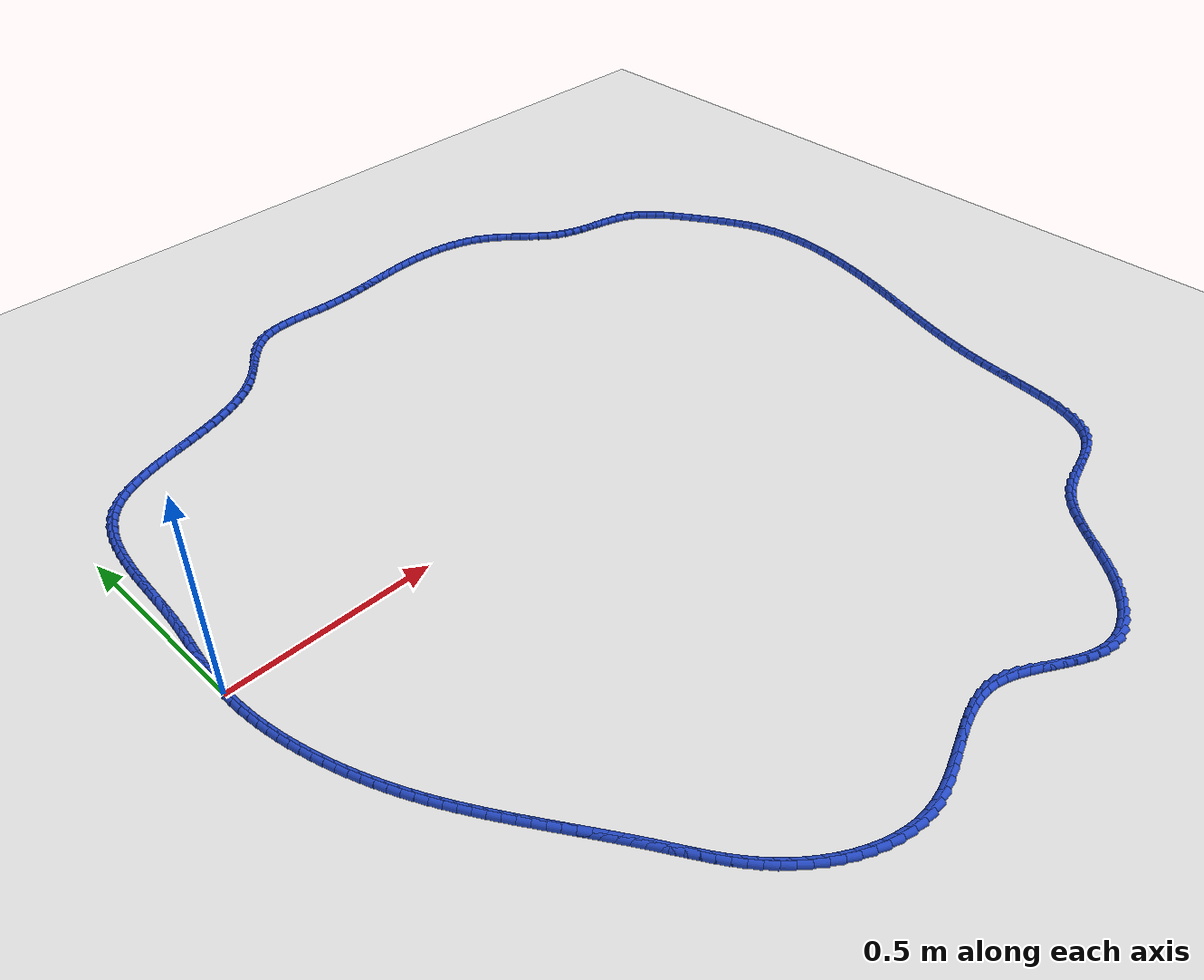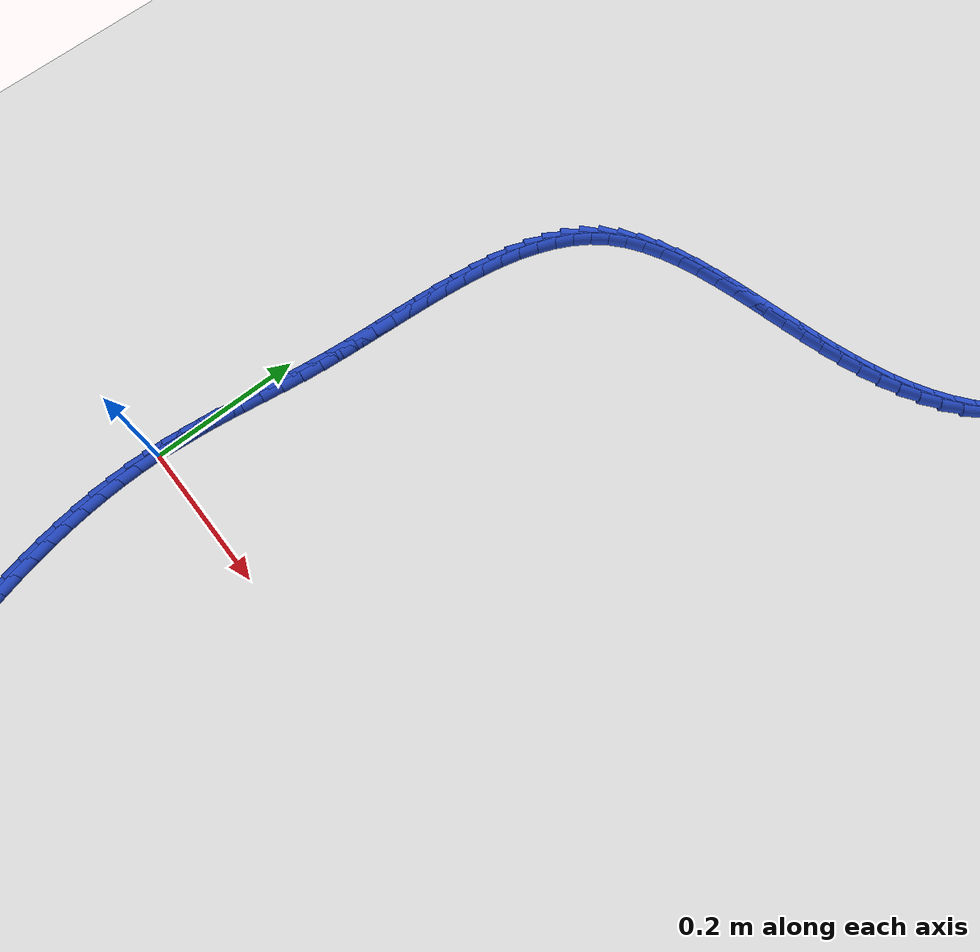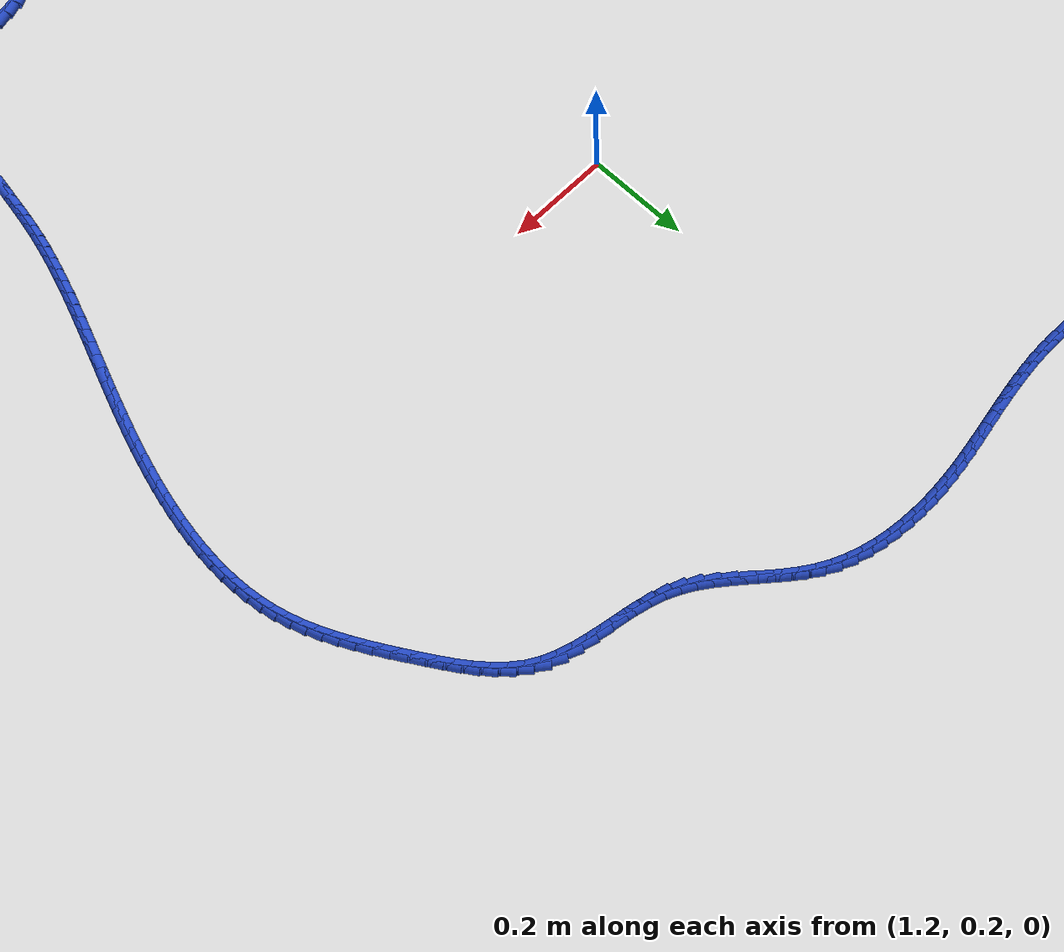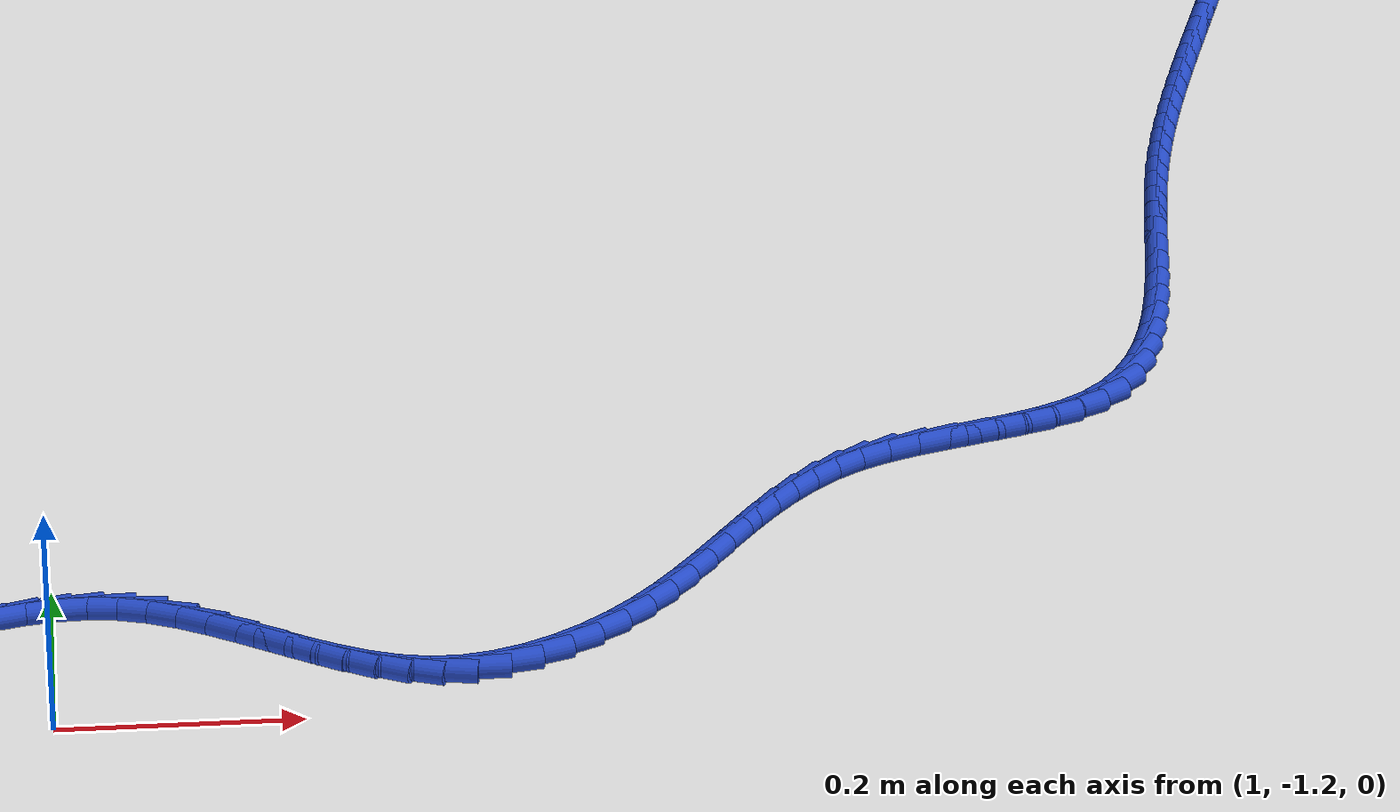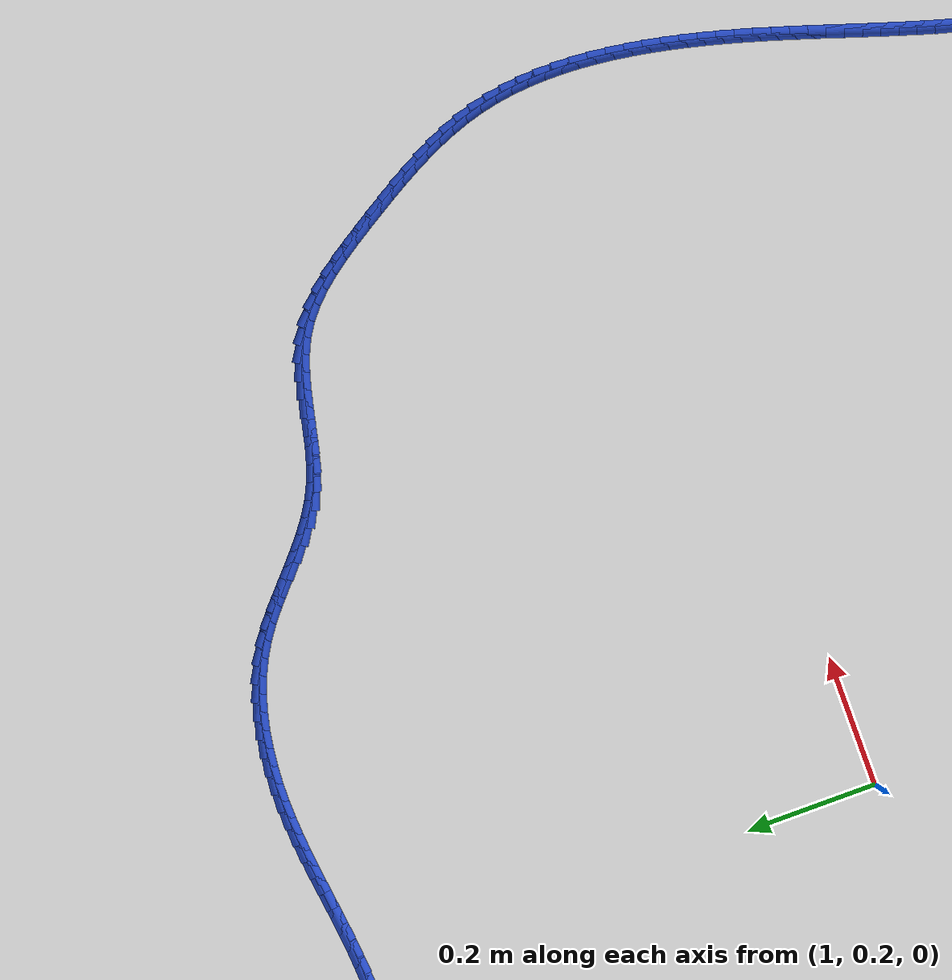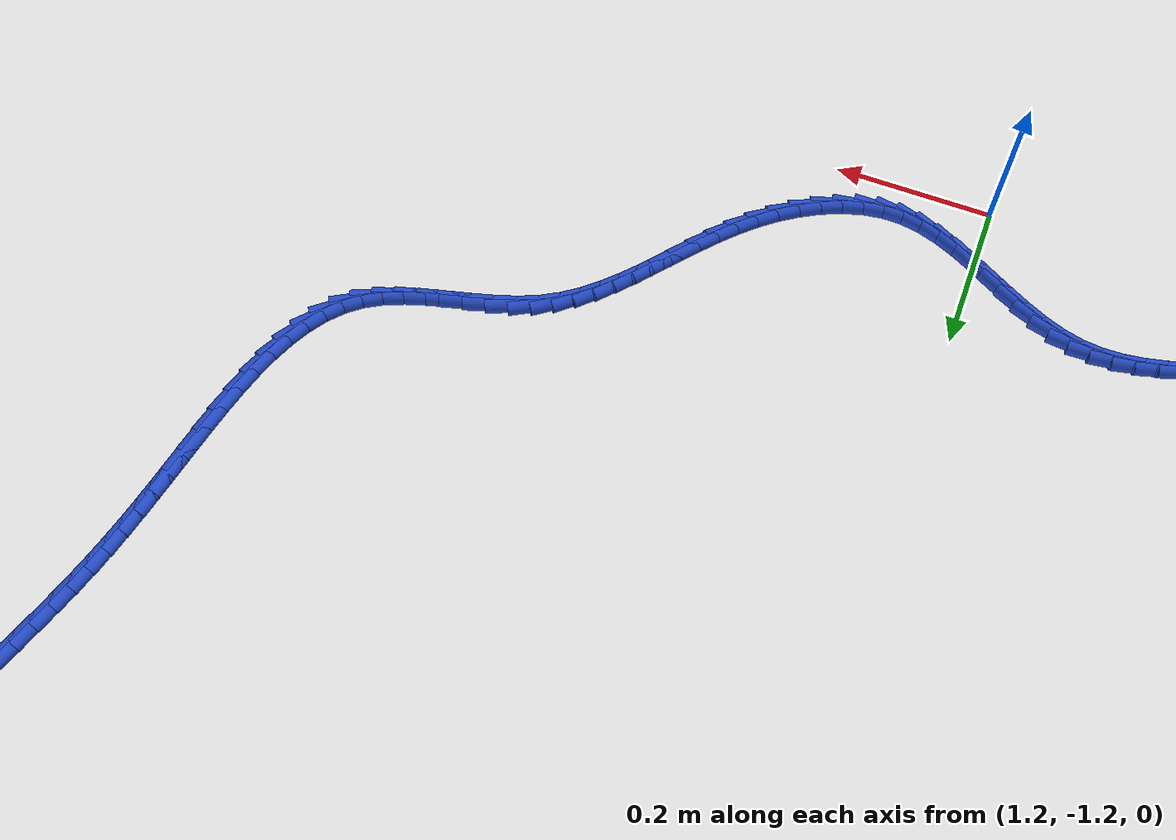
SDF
<sdf version="1.6">
 <world name="default">
  <light name="sun" type="directional">
   <pose>0 0 10 0 -0 0</pose>
   <diffuse>0.8 0.8 0.8 1</diffuse>
   <specular>0.2 0.2 0.2 1</specular>
   <attenuation>
    <range>1000</range>
    <constant>0.9</constant>
    <linear>0.01</linear>
    <quadratic>0.001</quadratic>
   </attenuation>
   <direction>-0.5 0.1 -0.9</direction>
  </light>
  <model name="ground_plane">
   <static>1</static>
   <link name="link">
    <collision name="collision">
     <geometry><plane><normal>0 0 1</normal><size>100 100</size></plane></geometry>
     <surface><friction><ode><mu>100</mu><mu2>50</mu2></ode></friction></surface>
    </collision>
    <visual name="visual">
     <cast_shadows>0</cast_shadows>
     <geometry><plane><normal>0 0 1</normal><size>100 100</size></plane></geometry>
     <material>
      <script><uri>file://media/materials/scripts/gazebo.material</uri><name>Gazebo/WhiteGlow</name></script>
     </material>
    </visual>
   </link>
  </model>
  <gravity>0 0 -9.8</gravity>
  <magnetic_field>6e-06 2.3e-05 -4.2e-05</magnetic_field>
  <atmosphere type="adiabatic"/>
  <physics name="default_physics" default="0" type="ode">
   <max_step_size>0.001</max_step_size>
   <real_time_factor>1</real_time_factor>
   <real_time_update_rate>1000</real_time_update_rate>
  </physics>
  <scene><ambient>0.4 0.4 0.4 1</ambient><background>0.7 0.7 0.7 1</background><shadows>1</shadows></scene>
  <spherical_coordinates>
   <surface_model>EARTH_WGS84</surface_model>
   <latitude_deg>0</latitude_deg>
   <longitude_deg>0</longitude_deg>
   <elevation>0</elevation>
   <heading_deg>0</heading_deg>
  </spherical_coordinates>
  <model name="line">
   <link name="link_0">
    <pose>7.806255641895632e-18 1.3877787807814457e-17 0.01 0 1.57 1.514587896362002</pose>
    <collision name="collision">
     <geometry><cylinder><radius>0.01</radius><length>0.08</length></cylinder></geometry>
    </collision>
    <visual name="visual">
     <material>
      <script><name>Gazebo/Blue</name><uri>file://media/materials/scripts/gazebo.material</uri></script>
     </material>
     <geometry><cylinder><radius>0.01</radius><length>0.08</length></cylinder></geometry>
    </visual>
   </link>
   <link name="link_1">
    <pose>0.0014770493484000506 0.026250394922614786 0.01 0 1.57 1.4805047317773097</pose>
    <collision name="collision">
     <geometry><cylinder><radius>0.01</radius><length>0.08</length></cylinder></geometry>
    </collision>
    <visual name="visual">
     <material>
      <script><name>Gazebo/Blue</name><uri>file://media/materials/scripts/gazebo.material</uri></script>
     </material>
     <geometry><cylinder><radius>0.01</radius><length>0.08</length></cylinder></geometry>
    </visual>
   </link>
   <link name="link_2">
    <pose>0.0038420901585894352 0.0523725412709468 0.01 0 1.57 1.454021096162606</pose>
    <collision name="collision">
     <geometry><cylinder><radius>0.01</radius><length>0.08</length></cylinder></geometry>
    </collision>
    <visual name="visual">
     <material>
      <script><name>Gazebo/Blue</name><uri>file://media/materials/scripts/gazebo.material</uri></script>
     </material>
     <geometry><cylinder><radius>0.01</radius><length>0.08</length></cylinder></geometry>
    </visual>
   </link>
   <link name="link_3">
    <pose>0.00690294590006227 0.07846480404666 0.01 0 1.57 1.4353766958146992</pose>
    <collision name="collision">
     <geometry><cylinder><radius>0.01</radius><length>0.08</length></cylinder></geometry>
    </collision>
    <visual name="visual">
     <material>
      <script><name>Gazebo/Blue</name><uri>file://media/materials/scripts/gazebo.material</uri></script>
     </material>
     <geometry><cylinder><radius>0.01</radius><length>0.08</length></cylinder></geometry>
    </visual>
   </link>
   <link name="link_4">
    <pose>0.010467440042312667 0.10462554825141833 0.01 0 1.57 1.424626006290899</pose>
    <collision name="collision">
     <geometry><cylinder><radius>0.01</radius><length>0.08</length></cylinder></geometry>
    </collision>
    <visual name="visual">
     <material>
      <script><name>Gazebo/Blue</name><uri>file://media/materials/scripts/gazebo.material</uri></script>
     </material>
     <geometry><cylinder><radius>0.01</radius><length>0.08</length></cylinder></geometry>
    </visual>
   </link>
   <link name="link_5">
    <pose>0.014343396054834737 0.13095313888688573 0.01 0 1.57 1.421673920319607</pose>
    <collision name="collision">
     <geometry><cylinder><radius>0.01</radius><length>0.08</length></cylinder></geometry>
    </collision>
    <visual name="visual">
     <material>
      <script><name>Gazebo/Blue</name><uri>file://media/materials/scripts/gazebo.material</uri></script>
     </material>
     <geometry><cylinder><radius>0.01</radius><length>0.08</length></cylinder></geometry>
    </visual>
   </link>
   <link name="link_6">
    <pose>0.018338637407122587 0.15754594095472613 0.01 0 1.57 1.4263030760799773</pose>
    <collision name="collision">
     <geometry><cylinder><radius>0.01</radius><length>0.08</length></cylinder></geometry>
    </collision>
    <visual name="visual">
     <material>
      <script><name>Gazebo/Blue</name><uri>file://media/materials/scripts/gazebo.material</uri></script>
     </material>
     <geometry><cylinder><radius>0.01</radius><length>0.08</length></cylinder></geometry>
    </visual>
   </link>
   <link name="link_7">
    <pose>0.02226098756867033 0.18450231945660348 0.01 0 1.57 1.4381908114511264</pose>
    <collision name="collision">
     <geometry><cylinder><radius>0.01</radius><length>0.08</length></cylinder></geometry>
    </collision>
    <visual name="visual">
     <material>
      <script><name>Gazebo/Blue</name><uri>file://media/materials/scripts/gazebo.material</uri></script>
     </material>
     <geometry><cylinder><radius>0.01</radius><length>0.08</length></cylinder></geometry>
    </visual>
   </link>
   <link name="link_8">
    <pose>0.025918270008972077 0.21192063939418174 0.01 0 1.57 1.456916770432809</pose>
    <collision name="collision">
     <geometry><cylinder><radius>0.01</radius><length>0.08</length></cylinder></geometry>
    </collision>
    <visual name="visual">
     <material>
      <script><name>Gazebo/Blue</name><uri>file://media/materials/scripts/gazebo.material</uri></script>
     </material>
     <geometry><cylinder><radius>0.01</radius><length>0.08</length></cylinder></geometry>
    </visual>
   </link>
   <link name="link_9">
    <pose>0.029118308786755177 0.23989926535403608 0.01 0 1.57 1.4793346312724578</pose>
    <collision name="collision">
     <geometry><cylinder><radius>0.01</radius><length>0.08</length></cylinder></geometry>
    </collision>
    <visual name="visual">
     <material>
      <script><name>Gazebo/Blue</name><uri>file://media/materials/scripts/gazebo.material</uri></script>
     </material>
     <geometry><cylinder><radius>0.01</radius><length>0.08</length></cylinder></geometry>
    </visual>
   </link>
   <link name="link_10">
    <pose>0.031740244625666 0.26848632249421284 0.01 0 1.57 1.4955250086959533</pose>
    <collision name="collision">
     <geometry><cylinder><radius>0.01</radius><length>0.08</length></cylinder></geometry>
    </collision>
    <visual name="visual">
     <material>
      <script><name>Gazebo/Blue</name><uri>file://media/materials/scripts/gazebo.material</uri></script>
     </material>
     <geometry><cylinder><radius>0.01</radius><length>0.08</length></cylinder></geometry>
    </visual>
   </link>
   <link name="link_11">
    <pose>0.033931370791312906 0.2975410343957975 0.01 0 1.57 1.5037256005084356</pose>
    <collision name="collision">
     <geometry><cylinder><radius>0.01</radius><length>0.08</length></cylinder></geometry>
    </collision>
    <visual name="visual">
     <material>
      <script><name>Gazebo/Blue</name><uri>file://media/materials/scripts/gazebo.material</uri></script>
     </material>
     <geometry><cylinder><radius>0.01</radius><length>0.08</length></cylinder></geometry>
    </visual>
   </link>
   <link name="link_12">
    <pose>0.03590199393413775 0.32687823450403164 0.01 0 1.57 1.5042915713219993</pose>
    <collision name="collision">
     <geometry><cylinder><radius>0.01</radius><length>0.08</length></cylinder></geometry>
    </collision>
    <visual name="visual">
     <material>
      <script><name>Gazebo/Blue</name><uri>file://media/materials/scripts/gazebo.material</uri></script>
     </material>
     <geometry><cylinder><radius>0.01</radius><length>0.08</length></cylinder></geometry>
    </visual>
   </link>
   <link name="link_13">
    <pose>0.037862420704582345 0.35631275626415665 0.01 0 1.57 1.497307724409378</pose>
    <collision name="collision">
     <geometry><cylinder><radius>0.01</radius><length>0.08</length></cylinder></geometry>
    </collision>
    <visual name="visual">
     <material>
      <script><name>Gazebo/Blue</name><uri>file://media/materials/scripts/gazebo.material</uri></script>
     </material>
     <geometry><cylinder><radius>0.01</radius><length>0.08</length></cylinder></geometry>
    </visual>
   </link>
   <link name="link_14">
    <pose>0.04002295775308848 0.38565943312141393 0.01 0 1.57 1.4825967873798298</pose>
    <collision name="collision">
     <geometry><cylinder><radius>0.01</radius><length>0.08</length></cylinder></geometry>
    </collision>
    <visual name="visual">
     <material>
      <script><name>Gazebo/Blue</name><uri>file://media/materials/scripts/gazebo.material</uri></script>
     </material>
     <geometry><cylinder><radius>0.01</radius><length>0.08</length></cylinder></geometry>
    </visual>
   </link>
   <link name="link_15">
    <pose>0.04259391173009801 0.41473309852104495 0.01 0 1.57 1.4597187084186494</pose>
    <collision name="collision">
     <geometry><cylinder><radius>0.01</radius><length>0.08</length></cylinder></geometry>
    </collision>
    <visual name="visual">
     <material>
      <script><name>Gazebo/Blue</name><uri>file://media/materials/scripts/gazebo.material</uri></script>
     </material>
     <geometry><cylinder><radius>0.01</radius><length>0.08</length></cylinder></geometry>
    </visual>
   </link>
   <link name="link_16">
    <pose>0.045785589286052725 0.443348585908291 0.01 0 1.57 1.4279644087267036</pose>
    <collision name="collision">
     <geometry><cylinder><radius>0.01</radius><length>0.08</length></cylinder></geometry>
    </collision>
    <visual name="visual">
     <material>
      <script><name>Gazebo/Blue</name><uri>file://media/materials/scripts/gazebo.material</uri></script>
     </material>
     <geometry><cylinder><radius>0.01</radius><length>0.08</length></cylinder></geometry>
    </visual>
   </link>
   <link name="link_17">
    <pose>0.049808297071394475 0.47132072872839387 0.01 0 1.57 1.3863520234284576</pose>
    <collision name="collision">
     <geometry><cylinder><radius>0.01</radius><length>0.08</length></cylinder></geometry>
    </collision>
    <visual name="visual">
     <material>
      <script><name>Gazebo/Blue</name><uri>file://media/materials/scripts/gazebo.material</uri></script>
     </material>
     <geometry><cylinder><radius>0.01</radius><length>0.08</length></cylinder></geometry>
    </visual>
   </link>
   <link name="link_18">
    <pose>0.05487234173656505 0.4984643604265946 0.01 0 1.57 1.3336417228431299</pose>
    <collision name="collision">
     <geometry><cylinder><radius>0.01</radius><length>0.08</length></cylinder></geometry>
    </collision>
    <visual name="visual">
     <material>
      <script><name>Gazebo/Blue</name><uri>file://media/materials/scripts/gazebo.material</uri></script>
     </material>
     <geometry><cylinder><radius>0.01</radius><length>0.08</length></cylinder></geometry>
    </visual>
   </link>
   <link name="link_19">
    <pose>0.061188029932006276 0.5245943144481348 0.01 0 1.57 1.2683987625830184</pose>
    <collision name="collision">
     <geometry><cylinder><radius>0.01</radius><length>0.08</length></cylinder></geometry>
    </collision>
    <visual name="visual">
     <material>
      <script><name>Gazebo/Blue</name><uri>file://media/materials/scripts/gazebo.material</uri></script>
     </material>
     <geometry><cylinder><radius>0.01</radius><length>0.08</length></cylinder></geometry>
    </visual>
   </link>
   <link name="link_20">
    <pose>0.06896566830815998 0.5495254242382557 0.01 0 1.57 1.1891535085259686</pose>
    <collision name="collision">
     <geometry><cylinder><radius>0.01</radius><length>0.08</length></cylinder></geometry>
    </collision>
    <visual name="visual">
     <material>
      <script><name>Gazebo/Blue</name><uri>file://media/materials/scripts/gazebo.material</uri></script>
     </material>
     <geometry><cylinder><radius>0.01</radius><length>0.08</length></cylinder></geometry>
    </visual>
   </link>
   <link name="link_21">
    <pose>0.07841556351546797 0.5730725232421989 0.01 0 1.57 1.0947236597595906</pose>
    <collision name="collision">
     <geometry><cylinder><radius>0.01</radius><length>0.08</length></cylinder></geometry>
    </collision>
    <visual name="visual">
     <material>
      <script><name>Gazebo/Blue</name><uri>file://media/materials/scripts/gazebo.material</uri></script>
     </material>
     <geometry><cylinder><radius>0.01</radius><length>0.08</length></cylinder></geometry>
    </visual>
   </link>
   <link name="link_22">
    <pose>0.08974802220437207 0.5950504449052061 0.01 0 1.57 0.9847494606015553</pose>
    <collision name="collision">
     <geometry><cylinder><radius>0.01</radius><length>0.08</length></cylinder></geometry>
    </collision>
    <visual name="visual">
     <material>
      <script><name>Gazebo/Blue</name><uri>file://media/materials/scripts/gazebo.material</uri></script>
     </material>
     <geometry><cylinder><radius>0.01</radius><length>0.08</length></cylinder></geometry>
    </visual>
   </link>
   <link name="link_23">
    <pose>0.10317335102531411 0.6152740226725182 0.01 0 1.57 0.8603930453724324</pose>
    <collision name="collision">
     <geometry><cylinder><radius>0.01</radius><length>0.08</length></cylinder></geometry>
    </collision>
    <visual name="visual">
     <material>
      <script><name>Gazebo/Blue</name><uri>file://media/materials/scripts/gazebo.material</uri></script>
     </material>
     <geometry><cylinder><radius>0.01</radius><length>0.08</length></cylinder></geometry>
    </visual>
   </link>
   <link name="link_24">
    <pose>0.11890185662873592 0.6335580899893772 0.01 0 1.57 0.7275257642742753</pose>
    <collision name="collision">
     <geometry><cylinder><radius>0.01</radius><length>0.08</length></cylinder></geometry>
    </collision>
    <visual name="visual">
     <material>
      <script><name>Gazebo/Blue</name><uri>file://media/materials/scripts/gazebo.material</uri></script>
     </material>
     <geometry><cylinder><radius>0.01</radius><length>0.08</length></cylinder></geometry>
    </visual>
   </link>
   <link name="link_25">
    <pose>0.13709441036242065 0.6497580418643729 0.01 0 1.57 0.6076032303712647</pose>
    <collision name="collision">
     <geometry><cylinder><radius>0.01</radius><length>0.08</length></cylinder></geometry>
    </collision>
    <visual name="visual">
     <material>
      <script><name>Gazebo/Blue</name><uri>file://media/materials/scripts/gazebo.material</uri></script>
     </material>
     <geometry><cylinder><radius>0.01</radius><length>0.08</length></cylinder></geometry>
    </visual>
   </link>
   <link name="link_26">
    <pose>0.15757916730137017 0.6640022663181729 0.01 0 1.57 0.5087072947108857</pose>
    <collision name="collision">
     <geometry><cylinder><radius>0.01</radius><length>0.08</length></cylinder></geometry>
    </collision>
    <visual name="visual">
     <material>
      <script><name>Gazebo/Blue</name><uri>file://media/materials/scripts/gazebo.material</uri></script>
     </material>
     <geometry><cylinder><radius>0.01</radius><length>0.08</length></cylinder></geometry>
    </visual>
   </link>
   <link name="link_27">
    <pose>0.18004703717224638 0.6765317608952389 0.01 0 1.57 0.4294636729440346</pose>
    <collision name="collision">
     <geometry><cylinder><radius>0.01</radius><length>0.08</length></cylinder></geometry>
    </collision>
    <visual name="visual">
     <material>
      <script><name>Gazebo/Blue</name><uri>file://media/materials/scripts/gazebo.material</uri></script>
     </material>
     <geometry><cylinder><radius>0.01</radius><length>0.08</length></cylinder></geometry>
    </visual>
   </link>
   <link name="link_28">
    <pose>0.204188499708276 0.6875878759487554 0.01 0 1.57 0.3676609509822385</pose>
    <collision name="collision">
     <geometry><cylinder><radius>0.01</radius><length>0.08</length></cylinder></geometry>
    </collision>
    <visual name="visual">
     <material>
      <script><name>Gazebo/Blue</name><uri>file://media/materials/scripts/gazebo.material</uri></script>
     </material>
     <geometry><cylinder><radius>0.01</radius><length>0.08</length></cylinder></geometry>
    </visual>
   </link>
   <link name="link_29">
    <pose>0.22969403464268548 0.6974119618319061 0.01 0 1.57 0.3210742084700685</pose>
    <collision name="collision">
     <geometry><cylinder><radius>0.01</radius><length>0.08</length></cylinder></geometry>
    </collision>
    <visual name="visual">
     <material>
      <script><name>Gazebo/Blue</name><uri>file://media/materials/scripts/gazebo.material</uri></script>
     </material>
     <geometry><cylinder><radius>0.01</radius><length>0.08</length></cylinder></geometry>
    </visual>
   </link>
   <link name="link_30">
    <pose>0.25625412170870177 0.7062453688978766 0.01 0 1.57 0.287842419389166</pose>
    <collision name="collision">
     <geometry><cylinder><radius>0.01</radius><length>0.08</length></cylinder></geometry>
    </collision>
    <visual name="visual">
     <material>
      <script><name>Gazebo/Blue</name><uri>file://media/materials/scripts/gazebo.material</uri></script>
     </material>
     <geometry><cylinder><radius>0.01</radius><length>0.08</length></cylinder></geometry>
    </visual>
   </link>
   <link name="link_31">
    <pose>0.2835592406395512 0.7143294474998498 0.01 0 1.57 0.2666034444324147</pose>
    <collision name="collision">
     <geometry><cylinder><radius>0.01</radius><length>0.08</length></cylinder></geometry>
    </collision>
    <visual name="visual">
     <material>
      <script><name>Gazebo/Blue</name><uri>file://media/materials/scripts/gazebo.material</uri></script>
     </material>
     <geometry><cylinder><radius>0.01</radius><length>0.08</length></cylinder></geometry>
    </visual>
   </link>
   <link name="link_32">
    <pose>0.31129987116846064 0.7219055479910109 0.01 0 1.57 0.2565231554013573</pose>
    <collision name="collision">
     <geometry><cylinder><radius>0.01</radius><length>0.08</length></cylinder></geometry>
    </collision>
    <visual name="visual">
     <material>
      <script><name>Gazebo/Blue</name><uri>file://media/materials/scripts/gazebo.material</uri></script>
     </material>
     <geometry><cylinder><radius>0.01</radius><length>0.08</length></cylinder></geometry>
    </visual>
   </link>
   <link name="link_33">
    <pose>0.3391664930286564 0.7292150207245438 0.01 0 1.57 0.25721990161455327</pose>
    <collision name="collision">
     <geometry><cylinder><radius>0.01</radius><length>0.08</length></cylinder></geometry>
    </collision>
    <visual name="visual">
     <material>
      <script><name>Gazebo/Blue</name><uri>file://media/materials/scripts/gazebo.material</uri></script>
     </material>
     <geometry><cylinder><radius>0.01</radius><length>0.08</length></cylinder></geometry>
    </visual>
   </link>
   <link name="link_34">
    <pose>0.3668546720123698 0.7364983102377841 0.01 0 1.57 0.26726730462012144</pose>
    <collision name="collision">
     <geometry><cylinder><radius>0.01</radius><length>0.08</length></cylinder></geometry>
    </collision>
    <visual name="visual">
     <material>
      <script><name>Gazebo/Blue</name><uri>file://media/materials/scripts/gazebo.material</uri></script>
     </material>
     <geometry><cylinder><radius>0.01</radius><length>0.08</length></cylinder></geometry>
    </visual>
   </link>
   <link name="link_35">
    <pose>0.3941667195460615 0.7439768499069268 0.01 0 1.57 0.2854745074267307</pose>
    <collision name="collision">
     <geometry><cylinder><radius>0.01</radius><length>0.08</length></cylinder></geometry>
    </collision>
    <visual name="visual">
     <material>
      <script><name>Gazebo/Blue</name><uri>file://media/materials/scripts/gazebo.material</uri></script>
     </material>
     <geometry><cylinder><radius>0.01</radius><length>0.08</length></cylinder></geometry>
    </visual>
   </link>
   <link name="link_36">
    <pose>0.4210062990281519 0.7518540225463364 0.01 0 1.57 0.31213653816001685</pose>
    <collision name="collision">
     <geometry><cylinder><radius>0.01</radius><length>0.08</length></cylinder></geometry>
    </collision>
    <visual name="visual">
     <material>
      <script><name>Gazebo/Blue</name><uri>file://media/materials/scripts/gazebo.material</uri></script>
     </material>
     <geometry><cylinder><radius>0.01</radius><length>0.08</length></cylinder></geometry>
    </visual>
   </link>
   <link name="link_37">
    <pose>0.44728108027442864 0.7603324974363145 0.01 0 1.57 0.3476306047556478</pose>
    <collision name="collision">
     <geometry><cylinder><radius>0.01</radius><length>0.08</length></cylinder></geometry>
    </collision>
    <visual name="visual">
     <material>
      <script><name>Gazebo/Blue</name><uri>file://media/materials/scripts/gazebo.material</uri></script>
     </material>
     <geometry><cylinder><radius>0.01</radius><length>0.08</length></cylinder></geometry>
    </visual>
   </link>
   <link name="link_38">
    <pose>0.472898733100679 0.7696149438571622 0.01 0 1.57 0.39229894244862284</pose>
    <collision name="collision">
     <geometry><cylinder><radius>0.01</radius><length>0.08</length></cylinder></geometry>
    </collision>
    <visual name="visual">
     <material>
      <script><name>Gazebo/Blue</name><uri>file://media/materials/scripts/gazebo.material</uri></script>
     </material>
     <geometry><cylinder><radius>0.01</radius><length>0.08</length></cylinder></geometry>
    </visual>
   </link>
   <link name="link_39">
    <pose>0.4977669273226901 0.7799040310891805 0.01 0 1.57 0.4463598285599928</pose>
    <collision name="collision">
     <geometry><cylinder><radius>0.01</radius><length>0.08</length></cylinder></geometry>
    </collision>
    <visual name="visual">
     <material>
      <script><name>Gazebo/Blue</name><uri>file://media/materials/scripts/gazebo.material</uri></script>
     </material>
     <geometry><cylinder><radius>0.01</radius><length>0.08</length></cylinder></geometry>
    </visual>
   </link>
   <link name="link_40">
    <pose>0.5217933327562492 0.7914024284126709 0.01 0 1.57 0.5097857412527896</pose>
    <collision name="collision">
     <geometry><cylinder><radius>0.01</radius><length>0.08</length></cylinder></geometry>
    </collision>
    <visual name="visual">
     <material>
      <script><name>Gazebo/Blue</name><uri>file://media/materials/scripts/gazebo.material</uri></script>
     </material>
     <geometry><cylinder><radius>0.01</radius><length>0.08</length></cylinder></geometry>
    </visual>
   </link>
   <link name="link_41">
    <pose>0.5448856192171434 0.8043128051079345 0.01 0 1.57 0.5821589660289005</pose>
    <collision name="collision">
     <geometry><cylinder><radius>0.01</radius><length>0.08</length></cylinder></geometry>
    </collision>
    <visual name="visual">
     <material>
      <script><name>Gazebo/Blue</name><uri>file://media/materials/scripts/gazebo.material</uri></script>
     </material>
     <geometry><cylinder><radius>0.01</radius><length>0.08</length></cylinder></geometry>
    </visual>
   </link>
   <link name="link_42">
    <pose>0.5669514565211606 0.8188378304552729 0.01 0 1.57 0.6625342673406417</pose>
    <collision name="collision">
     <geometry><cylinder><radius>0.01</radius><length>0.08</length></cylinder></geometry>
    </collision>
    <visual name="visual">
     <material>
      <script><name>Gazebo/Blue</name><uri>file://media/materials/scripts/gazebo.material</uri></script>
     </material>
     <geometry><cylinder><radius>0.01</radius><length>0.08</length></cylinder></geometry>
    </visual>
   </link>
   <link name="link_43">
    <pose>0.5878985144840875 0.835180173734987 0.01 0 1.57 0.7493516338687485</pose>
    <collision name="collision">
     <geometry><cylinder><radius>0.01</radius><length>0.08</length></cylinder></geometry>
    </collision>
    <visual name="visual">
     <material>
      <script><name>Gazebo/Blue</name><uri>file://media/materials/scripts/gazebo.material</uri></script>
     </material>
     <geometry><cylinder><radius>0.01</radius><length>0.08</length></cylinder></geometry>
    </visual>
   </link>
   <link name="link_44">
    <pose>0.6076345585165334 0.8535423152832421 0.01 0 1.57 0.8309043963542102</pose>
    <collision name="collision">
     <geometry><cylinder><radius>0.01</radius><length>0.08</length></cylinder></geometry>
    </collision>
    <visual name="visual">
     <material>
      <script><name>Gazebo/Blue</name><uri>file://media/materials/scripts/gazebo.material</uri></script>
     </material>
     <geometry><cylinder><radius>0.01</radius><length>0.08</length></cylinder></geometry>
    </visual>
   </link>
   <link name="link_45">
    <pose>0.6261952074169364 0.8738740319179299 0.01 0 1.57 0.879229027913659</pose>
    <collision name="collision">
     <geometry><cylinder><radius>0.01</radius><length>0.08</length></cylinder></geometry>
    </collision>
    <visual name="visual">
     <material>
      <script><name>Gazebo/Blue</name><uri>file://media/materials/scripts/gazebo.material</uri></script>
     </material>
     <geometry><cylinder><radius>0.01</radius><length>0.08</length></cylinder></geometry>
    </visual>
   </link>
   <link name="link_46">
    <pose>0.6439962974324887 0.8953735968117029 0.01 0 1.57 0.8919594255411456</pose>
    <collision name="collision">
     <geometry><cylinder><radius>0.01</radius><length>0.08</length></cylinder></geometry>
    </collision>
    <visual name="visual">
     <material>
      <script><name>Gazebo/Blue</name><uri>file://media/materials/scripts/gazebo.material</uri></script>
     </material>
     <geometry><cylinder><radius>0.01</radius><length>0.08</length></cylinder></geometry>
    </visual>
   </link>
   <link name="link_47">
    <pose>0.6615240226149033 0.9171002202227106 0.01 0 1.57 0.8696382455518886</pose>
    <collision name="collision">
     <geometry><cylinder><radius>0.01</radius><length>0.08</length></cylinder></geometry>
    </collision>
    <visual name="visual">
     <material>
      <script><name>Gazebo/Blue</name><uri>file://media/materials/scripts/gazebo.material</uri></script>
     </material>
     <geometry><cylinder><radius>0.01</radius><length>0.08</length></cylinder></geometry>
    </visual>
   </link>
   <link name="link_48">
    <pose>0.6792645770158923 0.9381131124091032 0.01 0 1.57 0.8097014040256388</pose>
    <collision name="collision">
     <geometry><cylinder><radius>0.01</radius><length>0.08</length></cylinder></geometry>
    </collision>
    <visual name="visual">
     <material>
      <script><name>Gazebo/Blue</name><uri>file://media/materials/scripts/gazebo.material</uri></script>
     </material>
     <geometry><cylinder><radius>0.01</radius><length>0.08</length></cylinder></geometry>
    </visual>
   </link>
   <link name="link_49">
    <pose>0.6977041546871692 0.9574714836290309 0.01 0 1.57 0.7069143886231135</pose>
    <collision name="collision">
     <geometry><cylinder><radius>0.01</radius><length>0.08</length></cylinder></geometry>
    </collision>
    <visual name="visual">
     <material>
      <script><name>Gazebo/Blue</name><uri>file://media/materials/scripts/gazebo.material</uri></script>
     </material>
     <geometry><cylinder><radius>0.01</radius><length>0.08</length></cylinder></geometry>
    </visual>
   </link>
   <link name="link_50">
    <pose>0.717328949680447 0.974234544140644 0.01 0 1.57 0.5558540827127091</pose>
    <collision name="collision">
     <geometry><cylinder><radius>0.01</radius><length>0.08</length></cylinder></geometry>
    </collision>
    <visual name="visual">
     <material>
      <script><name>Gazebo/Blue</name><uri>file://media/materials/scripts/gazebo.material</uri></script>
     </material>
     <geometry><cylinder><radius>0.01</radius><length>0.08</length></cylinder></geometry>
    </visual>
   </link>
   <link name="link_51">
    <pose>0.7386243958138554 0.9874630397553958 0.01 0 1.57 0.37677194231065686</pose>
    <collision name="collision">
     <geometry><cylinder><radius>0.01</radius><length>0.08</length></cylinder></geometry>
    </collision>
    <visual name="visual">
     <material>
      <script><name>Gazebo/Blue</name><uri>file://media/materials/scripts/gazebo.material</uri></script>
     </material>
     <geometry><cylinder><radius>0.01</radius><length>0.08</length></cylinder></geometry>
    </visual>
   </link>
   <link name="link_52">
    <pose>0.761858790825532 0.9966562973111617 0.01 0 1.57 0.22474269249002612</pose>
    <collision name="collision">
     <geometry><cylinder><radius>0.01</radius><length>0.08</length></cylinder></geometry>
    </collision>
    <visual name="visual">
     <material>
      <script><name>Gazebo/Blue</name><uri>file://media/materials/scripts/gazebo.material</uri></script>
     </material>
     <geometry><cylinder><radius>0.01</radius><length>0.08</length></cylinder></geometry>
    </visual>
   </link>
   <link name="link_53">
    <pose>0.7867850860380194 1.0023545630541533 0.01 0 1.57 0.10963350602497841</pose>
    <collision name="collision">
     <geometry><cylinder><radius>0.01</radius><length>0.08</length></cylinder></geometry>
    </collision>
    <visual name="visual">
     <material>
      <script><name>Gazebo/Blue</name><uri>file://media/materials/scripts/gazebo.material</uri></script>
     </material>
     <geometry><cylinder><radius>0.01</radius><length>0.08</length></cylinder></geometry>
    </visual>
   </link>
   <link name="link_54">
    <pose>0.8130814503490357 1.0052491320688905 0.01 0 1.57 0.028596289146574087</pose>
    <collision name="collision">
     <geometry><cylinder><radius>0.01</radius><length>0.08</length></cylinder></geometry>
    </collision>
    <visual name="visual">
     <material>
      <script><name>Gazebo/Blue</name><uri>file://media/materials/scripts/gazebo.material</uri></script>
     </material>
     <geometry><cylinder><radius>0.01</radius><length>0.08</length></cylinder></geometry>
    </visual>
   </link>
   <link name="link_55">
    <pose>0.8404260526562976 1.0060312994398946 0.01 0 1.57 -0.022757602899486928</pose>
    <collision name="collision">
     <geometry><cylinder><radius>0.01</radius><length>0.08</length></cylinder></geometry>
    </collision>
    <visual name="visual">
     <material>
      <script><name>Gazebo/Blue</name><uri>file://media/materials/scripts/gazebo.material</uri></script>
     </material>
     <geometry><cylinder><radius>0.01</radius><length>0.08</length></cylinder></geometry>
    </visual>
   </link>
   <link name="link_56">
    <pose>0.868497061857523 1.0053923602516865 0.01 0 1.57 -0.048030548358376585</pose>
    <collision name="collision">
     <geometry><cylinder><radius>0.01</radius><length>0.08</length></cylinder></geometry>
    </collision>
    <visual name="visual">
     <material>
      <script><name>Gazebo/Blue</name><uri>file://media/materials/scripts/gazebo.material</uri></script>
     </material>
     <geometry><cylinder><radius>0.01</radius><length>0.08</length></cylinder></geometry>
    </visual>
   </link>
   <link name="link_57">
    <pose>0.8969726468504292 1.0040236095887867 0.01 0 1.57 -0.04923711139930998</pose>
    <collision name="collision">
     <geometry><cylinder><radius>0.01</radius><length>0.08</length></cylinder></geometry>
    </collision>
    <visual name="visual">
     <material>
      <script><name>Gazebo/Blue</name><uri>file://media/materials/scripts/gazebo.material</uri></script>
     </material>
     <geometry><cylinder><radius>0.01</radius><length>0.08</length></cylinder></geometry>
    </visual>
   </link>
   <link name="link_58">
    <pose>0.9255309765327342 1.002616342535716 0.01 0 1.57 -0.026667314538624903</pose>
    <collision name="collision">
     <geometry><cylinder><radius>0.01</radius><length>0.08</length></cylinder></geometry>
    </collision>
    <visual name="visual">
     <material>
      <script><name>Gazebo/Blue</name><uri>file://media/materials/scripts/gazebo.material</uri></script>
     </material>
     <geometry><cylinder><radius>0.01</radius><length>0.08</length></cylinder></geometry>
    </visual>
   </link>
   <link name="link_59">
    <pose>0.953850614978977 1.0018609547575787 0.01 0 1.57 0.012464451421779411</pose>
    <collision name="collision">
     <geometry><cylinder><radius>0.01</radius><length>0.08</length></cylinder></geometry>
    </collision>
    <visual name="visual">
     <material>
      <script><name>Gazebo/Blue</name><uri>file://media/materials/scripts/gazebo.material</uri></script>
     </material>
     <geometry><cylinder><radius>0.01</radius><length>0.08</length></cylinder></geometry>
    </visual>
   </link>
   <link name="link_60">
    <pose>0.9817153771452888 1.0022082917198851 0.01 0 1.57 0.04880122276599813</pose>
    <collision name="collision">
     <geometry><cylinder><radius>0.01</radius><length>0.08</length></cylinder></geometry>
    </collision>
    <visual name="visual">
     <material>
      <script><name>Gazebo/Blue</name><uri>file://media/materials/scripts/gazebo.material</uri></script>
     </material>
     <geometry><cylinder><radius>0.01</radius><length>0.08</length></cylinder></geometry>
    </visual>
   </link>
   <link name="link_61">
    <pose>1.0091554470662898 1.0035484647543063 0.01 0 1.57 0.07896925969057088</pose>
    <collision name="collision">
     <geometry><cylinder><radius>0.01</radius><length>0.08</length></cylinder></geometry>
    </collision>
    <visual name="visual">
     <material>
      <script><name>Gazebo/Blue</name><uri>file://media/materials/scripts/gazebo.material</uri></script>
     </material>
     <geometry><cylinder><radius>0.01</radius><length>0.08</length></cylinder></geometry>
    </visual>
   </link>
   <link name="link_62">
    <pose>1.036236209310111 1.0056914690481047 0.01 0 1.57 0.10251934402903636</pose>
    <collision name="collision">
     <geometry><cylinder><radius>0.01</radius><length>0.08</length></cylinder></geometry>
    </collision>
    <visual name="visual">
     <material>
      <script><name>Gazebo/Blue</name><uri>file://media/materials/scripts/gazebo.material</uri></script>
     </material>
     <geometry><cylinder><radius>0.01</radius><length>0.08</length></cylinder></geometry>
    </visual>
   </link>
   <link name="link_63">
    <pose>1.0630230484448846 1.0084472997885436 0.01 0 1.57 0.11911920896090153</pose>
    <collision name="collision">
     <geometry><cylinder><radius>0.01</radius><length>0.08</length></cylinder></geometry>
    </collision>
    <visual name="visual">
     <material>
      <script><name>Gazebo/Blue</name><uri>file://media/materials/scripts/gazebo.material</uri></script>
     </material>
     <geometry><cylinder><radius>0.01</radius><length>0.08</length></cylinder></geometry>
    </visual>
   </link>
   <link name="link_64">
    <pose>1.089581349038742 1.011625952162886 0.01 0 1.57 0.12853354086852745</pose>
    <collision name="collision">
     <geometry><cylinder><radius>0.01</radius><length>0.08</length></cylinder></geometry>
    </collision>
    <visual name="visual">
     <material>
      <script><name>Gazebo/Blue</name><uri>file://media/materials/scripts/gazebo.material</uri></script>
     </material>
     <geometry><cylinder><radius>0.01</radius><length>0.08</length></cylinder></geometry>
    </visual>
   </link>
   <link name="link_65">
    <pose>1.115976495659816 1.0150374213583953 0.01 0 1.57 0.13060685056808405</pose>
    <collision name="collision">
     <geometry><cylinder><radius>0.01</radius><length>0.08</length></cylinder></geometry>
    </collision>
    <visual name="visual">
     <material>
      <script><name>Gazebo/Blue</name><uri>file://media/materials/scripts/gazebo.material</uri></script>
     </material>
     <geometry><cylinder><radius>0.01</radius><length>0.08</length></cylinder></geometry>
    </visual>
   </link>
   <link name="link_66">
    <pose>1.142273872876237 1.0184917025623337 0.01 0 1.57 0.12525326299890907</pose>
    <collision name="collision">
     <geometry><cylinder><radius>0.01</radius><length>0.08</length></cylinder></geometry>
    </collision>
    <visual name="visual">
     <material>
      <script><name>Gazebo/Blue</name><uri>file://media/materials/scripts/gazebo.material</uri></script>
     </material>
     <geometry><cylinder><radius>0.01</radius><length>0.08</length></cylinder></geometry>
    </visual>
   </link>
   <link name="link_67">
    <pose>1.168538865256138 1.0217987909619648 0.01 0 1.57 0.1124557656931879</pose>
    <collision name="collision">
     <geometry><cylinder><radius>0.01</radius><length>0.08</length></cylinder></geometry>
    </collision>
    <visual name="visual">
     <material>
      <script><name>Gazebo/Blue</name><uri>file://media/materials/scripts/gazebo.material</uri></script>
     </material>
     <geometry><cylinder><radius>0.01</radius><length>0.08</length></cylinder></geometry>
    </visual>
   </link>
   <link name="link_68">
    <pose>1.1948368573676498 1.0247686817445516 0.01 0 1.57 0.0922759749259275</pose>
    <collision name="collision">
     <geometry><cylinder><radius>0.01</radius><length>0.08</length></cylinder></geometry>
    </collision>
    <visual name="visual">
     <material>
      <script><name>Gazebo/Blue</name><uri>file://media/materials/scripts/gazebo.material</uri></script>
     </material>
     <geometry><cylinder><radius>0.01</radius><length>0.08</length></cylinder></geometry>
    </visual>
   </link>
   <link name="link_69">
    <pose>1.2212332337789045 1.0272113700973566 0.01 0 1.57 0.06487388456592673</pose>
    <collision name="collision">
     <geometry><cylinder><radius>0.01</radius><length>0.08</length></cylinder></geometry>
    </collision>
    <visual name="visual">
     <material>
      <script><name>Gazebo/Blue</name><uri>file://media/materials/scripts/gazebo.material</uri></script>
     </material>
     <geometry><cylinder><radius>0.01</radius><length>0.08</length></cylinder></geometry>
    </visual>
   </link>
   <link name="link_70">
    <pose>1.2477933790580347 1.0289368512076433 0.01 0 1.57 0.030535130146066913</pose>
    <collision name="collision">
     <geometry><cylinder><radius>0.01</radius><length>0.08</length></cylinder></geometry>
    </collision>
    <visual name="visual">
     <material>
      <script><name>Gazebo/Blue</name><uri>file://media/materials/scripts/gazebo.material</uri></script>
     </material>
     <geometry><cylinder><radius>0.01</radius><length>0.08</length></cylinder></geometry>
    </visual>
   </link>
   <link name="link_71">
    <pose>1.274582677773171 1.0297551202626745 0.01 0 1.57 -0.010173157349849507</pose>
    <collision name="collision">
     <geometry><cylinder><radius>0.01</radius><length>0.08</length></cylinder></geometry>
    </collision>
    <visual name="visual">
     <material>
      <script><name>Gazebo/Blue</name><uri>file://media/materials/scripts/gazebo.material</uri></script>
     </material>
     <geometry><cylinder><radius>0.01</radius><length>0.08</length></cylinder></geometry>
    </visual>
   </link>
   <link name="link_72">
    <pose>1.3016534377618698 1.0294797156608357 0.01 0 1.57 -0.055532549233065845</pose>
    <collision name="collision">
     <geometry><cylinder><radius>0.01</radius><length>0.08</length></cylinder></geometry>
    </collision>
    <visual name="visual">
     <material>
      <script><name>Gazebo/Blue</name><uri>file://media/materials/scripts/gazebo.material</uri></script>
     </material>
     <geometry><cylinder><radius>0.01</radius><length>0.08</length></cylinder></geometry>
    </visual>
   </link>
   <link name="link_73">
    <pose>1.3289087779363626 1.0279645993495408 0.01 0 1.57 -0.10512822399784358</pose>
    <collision name="collision">
     <geometry><cylinder><radius>0.01</radius><length>0.08</length></cylinder></geometry>
    </collision>
    <visual name="visual">
     <material>
      <script><name>Gazebo/Blue</name><uri>file://media/materials/scripts/gazebo.material</uri></script>
     </material>
     <geometry><cylinder><radius>0.01</radius><length>0.08</length></cylinder></geometry>
    </visual>
   </link>
   <link name="link_74">
    <pose>1.3561568923669778 1.0250894536773143 0.01 0 1.57 -0.15964538687604257</pose>
    <collision name="collision">
     <geometry><cylinder><radius>0.01</radius><length>0.08</length></cylinder></geometry>
    </collision>
    <visual name="visual">
     <material>
      <script><name>Gazebo/Blue</name><uri>file://media/materials/scripts/gazebo.material</uri></script>
     </material>
     <geometry><cylinder><radius>0.01</radius><length>0.08</length></cylinder></geometry>
    </visual>
   </link>
   <link name="link_75">
    <pose>1.3832044515678463 1.0207343738085026 0.01 0 1.57 -0.21980845777226873</pose>
    <collision name="collision">
     <geometry><cylinder><radius>0.01</radius><length>0.08</length></cylinder></geometry>
    </collision>
    <visual name="visual">
     <material>
      <script><name>Gazebo/Blue</name><uri>file://media/materials/scripts/gazebo.material</uri></script>
     </material>
     <geometry><cylinder><radius>0.01</radius><length>0.08</length></cylinder></geometry>
    </visual>
   </link>
   <link name="link_76">
    <pose>1.4098581260530965 1.0147794549074514 0.01 0 1.57 -0.2863358960407748</pose>
    <collision name="collision">
     <geometry><cylinder><radius>0.01</radius><length>0.08</length></cylinder></geometry>
    </collision>
    <visual name="visual">
     <material>
      <script><name>Gazebo/Blue</name><uri>file://media/materials/scripts/gazebo.material</uri></script>
     </material>
     <geometry><cylinder><radius>0.01</radius><length>0.08</length></cylinder></geometry>
    </visual>
   </link>
   <link name="link_77">
    <pose>1.4359245863368595 1.0071047921385066 0.01 0 1.57 -0.3598829242569389</pose>
    <collision name="collision">
     <geometry><cylinder><radius>0.01</radius><length>0.08</length></cylinder></geometry>
    </collision>
    <visual name="visual">
     <material>
      <script><name>Gazebo/Blue</name><uri>file://media/materials/scripts/gazebo.material</uri></script>
     </material>
     <geometry><cylinder><radius>0.01</radius><length>0.08</length></cylinder></geometry>
    </visual>
   </link>
   <link name="link_78">
    <pose>1.4612105029332643 0.9975904806660139 0.01 0 1.57 -0.4409500118255547</pose>
    <collision name="collision">
     <geometry><cylinder><radius>0.01</radius><length>0.08</length></cylinder></geometry>
    </collision>
    <visual name="visual">
     <material>
      <script><name>Gazebo/Blue</name><uri>file://media/materials/scripts/gazebo.material</uri></script>
     </material>
     <geometry><cylinder><radius>0.01</radius><length>0.08</length></cylinder></geometry>
    </visual>
   </link>
   <link name="link_79">
    <pose>1.4855225463564412 0.9861166156543196 0.01 0 1.57 -0.5295961335737249</pose>
    <collision name="collision">
     <geometry><cylinder><radius>0.01</radius><length>0.08</length></cylinder></geometry>
    </collision>
    <visual name="visual">
     <material>
      <script><name>Gazebo/Blue</name><uri>file://media/materials/scripts/gazebo.material</uri></script>
     </material>
     <geometry><cylinder><radius>0.01</radius><length>0.08</length></cylinder></geometry>
    </visual>
   </link>
   <link name="link_80">
    <pose>1.5086699831194919 0.972566693478076 0.01 0 1.57 -0.6144212143440627</pose>
    <collision name="collision">
     <geometry><cylinder><radius>0.01</radius><length>0.08</length></cylinder></geometry>
    </collision>
    <visual name="visual">
     <material>
      <script><name>Gazebo/Blue</name><uri>file://media/materials/scripts/gazebo.material</uri></script>
     </material>
     <geometry><cylinder><radius>0.01</radius><length>0.08</length></cylinder></geometry>
    </visual>
   </link>
   <link name="link_81">
    <pose>1.5306445072200225 0.9570632222554469 0.01 0 1.57 -0.6767141334704676</pose>
    <collision name="collision">
     <geometry><cylinder><radius>0.01</radius><length>0.08</length></cylinder></geometry>
    </collision>
    <visual name="visual">
     <material>
      <script><name>Gazebo/Blue</name><uri>file://media/materials/scripts/gazebo.material</uri></script>
     </material>
     <geometry><cylinder><radius>0.01</radius><length>0.08</length></cylinder></geometry>
    </visual>
   </link>
   <link name="link_82">
    <pose>1.551737078750155 0.9401208007548525 0.01 0 1.57 -0.7151545196686331</pose>
    <collision name="collision">
     <geometry><cylinder><radius>0.01</radius><length>0.08</length></cylinder></geometry>
    </collision>
    <visual name="visual">
     <material>
      <script><name>Gazebo/Blue</name><uri>file://media/materials/scripts/gazebo.material</uri></script>
     </material>
     <geometry><cylinder><radius>0.01</radius><length>0.08</length></cylinder></geometry>
    </visual>
   </link>
   <link name="link_83">
    <pose>1.5722664315542965 0.9222904161922971 0.01 0 1.57 -0.7303852027726812</pose>
    <collision name="collision">
     <geometry><cylinder><radius>0.01</radius><length>0.08</length></cylinder></geometry>
    </collision>
    <visual name="visual">
     <material>
      <script><name>Gazebo/Blue</name><uri>file://media/materials/scripts/gazebo.material</uri></script>
     </material>
     <geometry><cylinder><radius>0.01</radius><length>0.08</length></cylinder></geometry>
    </visual>
   </link>
   <link name="link_84">
    <pose>1.5925512994768547 0.9041230557837867 0.01 0 1.57 -0.7226871563008217</pose>
    <collision name="collision">
     <geometry><cylinder><radius>0.01</radius><length>0.08</length></cylinder></geometry>
    </collision>
    <visual name="visual">
     <material>
      <script><name>Gazebo/Blue</name><uri>file://media/materials/scripts/gazebo.material</uri></script>
     </material>
     <geometry><cylinder><radius>0.01</radius><length>0.08</length></cylinder></geometry>
    </visual>
   </link>
   <link name="link_85">
    <pose>1.6129104163622379 0.8861697067453255 0.01 0 1.57 -0.6917428814139618</pose>
    <collision name="collision">
     <geometry><cylinder><radius>0.01</radius><length>0.08</length></cylinder></geometry>
    </collision>
    <visual name="visual">
     <material>
      <script><name>Gazebo/Blue</name><uri>file://media/materials/scripts/gazebo.material</uri></script>
     </material>
     <geometry><cylinder><radius>0.01</radius><length>0.08</length></cylinder></geometry>
    </visual>
   </link>
   <link name="link_86">
    <pose>1.6336625160548532 0.8689813562929182 0.01 0 1.57 -0.6367433298396322</pose>
    <collision name="collision">
     <geometry><cylinder><radius>0.01</radius><length>0.08</length></cylinder></geometry>
    </collision>
    <visual name="visual">
     <material>
      <script><name>Gazebo/Blue</name><uri>file://media/materials/scripts/gazebo.material</uri></script>
     </material>
     <geometry><cylinder><radius>0.01</radius><length>0.08</length></cylinder></geometry>
    </visual>
   </link>
   <link name="link_87">
    <pose>1.655126332399109 0.8531089916425703 0.01 0 1.57 -0.5568863828993236</pose>
    <collision name="collision">
     <geometry><cylinder><radius>0.01</radius><length>0.08</length></cylinder></geometry>
    </collision>
    <visual name="visual">
     <material>
      <script><name>Gazebo/Blue</name><uri>file://media/materials/scripts/gazebo.material</uri></script>
     </material>
     <geometry><cylinder><radius>0.01</radius><length>0.08</length></cylinder></geometry>
    </visual>
   </link>
   <link name="link_88">
    <pose>1.6776205992394129 0.8391036000102863 0.01 0 1.57 -0.45298381559977685</pose>
    <collision name="collision">
     <geometry><cylinder><radius>0.01</radius><length>0.08</length></cylinder></geometry>
    </collision>
    <visual name="visual">
     <material>
      <script><name>Gazebo/Blue</name><uri>file://media/materials/scripts/gazebo.material</uri></script>
     </material>
     <geometry><cylinder><radius>0.01</radius><length>0.08</length></cylinder></geometry>
    </visual>
   </link>
   <link name="link_89">
    <pose>1.7014558068835706 0.8275020402164774 0.01 0 1.57 -0.34952521857889296</pose>
    <collision name="collision">
     <geometry><cylinder><radius>0.01</radius><length>0.08</length></cylinder></geometry>
    </collision>
    <visual name="visual">
     <material>
      <script><name>Gazebo/Blue</name><uri>file://media/materials/scripts/gazebo.material</uri></script>
     </material>
     <geometry><cylinder><radius>0.01</radius><length>0.08</length></cylinder></geometry>
    </visual>
   </link>
   <link name="link_90">
    <pose>1.726639914867946 0.8183226709978724 0.01 0 1.57 -0.2755187125285224</pose>
    <collision name="collision">
     <geometry><cylinder><radius>0.01</radius><length>0.08</length></cylinder></geometry>
    </collision>
    <visual name="visual">
     <material>
      <script><name>Gazebo/Blue</name><uri>file://media/materials/scripts/gazebo.material</uri></script>
     </material>
     <geometry><cylinder><radius>0.01</radius><length>0.08</length></cylinder></geometry>
    </visual>
   </link>
   <link name="link_91">
    <pose>1.7527979573813182 0.8109275647113939 0.01 0 1.57 -0.23112465351206965</pose>
    <collision name="collision">
     <geometry><cylinder><radius>0.01</radius><length>0.08</length></cylinder></geometry>
    </collision>
    <visual name="visual">
     <material>
      <script><name>Gazebo/Blue</name><uri>file://media/materials/scripts/gazebo.material</uri></script>
     </material>
     <geometry><cylinder><radius>0.01</radius><length>0.08</length></cylinder></geometry>
    </visual>
   </link>
   <link name="link_92">
    <pose>1.7795303657285275 0.8046366274334308 0.01 0 1.57 -0.21468055850429885</pose>
    <collision name="collision">
     <geometry><cylinder><radius>0.01</radius><length>0.08</length></cylinder></geometry>
    </collision>
    <visual name="visual">
     <material>
      <script><name>Gazebo/Blue</name><uri>file://media/materials/scripts/gazebo.material</uri></script>
     </material>
     <geometry><cylinder><radius>0.01</radius><length>0.08</length></cylinder></geometry>
    </visual>
   </link>
   <link name="link_93">
    <pose>1.8064375712144176 0.7987697652403719 0.01 0 1.57 -0.22556719818584267</pose>
    <collision name="collision">
     <geometry><cylinder><radius>0.01</radius><length>0.08</length></cylinder></geometry>
    </collision>
    <visual name="visual">
     <material>
      <script><name>Gazebo/Blue</name><uri>file://media/materials/scripts/gazebo.material</uri></script>
     </material>
     <geometry><cylinder><radius>0.01</radius><length>0.08</length></cylinder></geometry>
    </visual>
   </link>
   <link name="link_94">
    <pose>1.8331200051438317 0.7926468842086055 0.01 0 1.57 -0.26454535174687444</pose>
    <collision name="collision">
     <geometry><cylinder><radius>0.01</radius><length>0.08</length></cylinder></geometry>
    </collision>
    <visual name="visual">
     <material>
      <script><name>Gazebo/Blue</name><uri>file://media/materials/scripts/gazebo.material</uri></script>
     </material>
     <geometry><cylinder><radius>0.01</radius><length>0.08</length></cylinder></geometry>
    </visual>
   </link>
   <link name="link_95">
    <pose>1.8591780988216113 0.7855878904145212 0.01 0 1.57 -0.33358389174459396</pose>
    <collision name="collision">
     <geometry><cylinder><radius>0.01</radius><length>0.08</length></cylinder></geometry>
    </collision>
    <visual name="visual">
     <material>
      <script><name>Gazebo/Blue</name><uri>file://media/materials/scripts/gazebo.material</uri></script>
     </material>
     <geometry><cylinder><radius>0.01</radius><length>0.08</length></cylinder></geometry>
    </visual>
   </link>
   <link name="link_96">
    <pose>1.8842122835525992 0.7769126899345067 0.01 0 1.57 -0.4349972386091499</pose>
    <collision name="collision">
     <geometry><cylinder><radius>0.01</radius><length>0.08</length></cylinder></geometry>
    </collision>
    <visual name="visual">
     <material>
      <script><name>Gazebo/Blue</name><uri>file://media/materials/scripts/gazebo.material</uri></script>
     </material>
     <geometry><cylinder><radius>0.01</radius><length>0.08</length></cylinder></geometry>
    </visual>
   </link>
   <link name="link_97">
    <pose>1.907822990641639 0.7659411888449517 0.01 0 1.57 -0.5657448975996008</pose>
    <collision name="collision">
     <geometry><cylinder><radius>0.01</radius><length>0.08</length></cylinder></geometry>
    </collision>
    <visual name="visual">
     <material>
      <script><name>Gazebo/Blue</name><uri>file://media/materials/scripts/gazebo.material</uri></script>
     </material>
     <geometry><cylinder><radius>0.01</radius><length>0.08</length></cylinder></geometry>
    </visual>
   </link>
   <link name="link_98">
    <pose>1.9296574332456284 0.7520767201389933 0.01 0 1.57 -0.6918289131424801</pose>
    <collision name="collision">
     <geometry><cylinder><radius>0.01</radius><length>0.08</length></cylinder></geometry>
    </collision>
    <visual name="visual">
     <material>
      <script><name>Gazebo/Blue</name><uri>file://media/materials/scripts/gazebo.material</uri></script>
     </material>
     <geometry><cylinder><radius>0.01</radius><length>0.08</length></cylinder></geometry>
    </visual>
   </link>
   <link name="link_99">
    <pose>1.949757141939537 0.7354258101414767 0.01 0 1.57 -0.7953502782584237</pose>
    <collision name="collision">
     <geometry><cylinder><radius>0.01</radius><length>0.08</length></cylinder></geometry>
    </collision>
    <visual name="visual">
     <material>
      <script><name>Gazebo/Blue</name><uri>file://media/materials/scripts/gazebo.material</uri></script>
     </material>
     <geometry><cylinder><radius>0.01</radius><length>0.08</length></cylinder></geometry>
    </visual>
   </link>
   <link name="link_100">
    <pose>1.968361354596024 0.7164475601510968 0.01 0 1.57 -0.8766369496641022</pose>
    <collision name="collision">
     <geometry><cylinder><radius>0.01</radius><length>0.08</length></cylinder></geometry>
    </collision>
    <visual name="visual">
     <material>
      <script><name>Gazebo/Blue</name><uri>file://media/materials/scripts/gazebo.material</uri></script>
     </material>
     <geometry><cylinder><radius>0.01</radius><length>0.08</length></cylinder></geometry>
    </visual>
   </link>
   <link name="link_101">
    <pose>1.9857107906393274 0.6956037135440767 0.01 0 1.57 -0.9374515009923445</pose>
    <collision name="collision">
     <geometry><cylinder><radius>0.01</radius><length>0.08</length></cylinder></geometry>
    </collision>
    <visual name="visual">
     <material>
      <script><name>Gazebo/Blue</name><uri>file://media/materials/scripts/gazebo.material</uri></script>
     </material>
     <geometry><cylinder><radius>0.01</radius><length>0.08</length></cylinder></geometry>
    </visual>
   </link>
   <link name="link_102">
    <pose>2.002046169493682 0.6733560136966384 0.01 0 1.57 -0.9797498041801713</pose>
    <collision name="collision">
     <geometry><cylinder><radius>0.01</radius><length>0.08</length></cylinder></geometry>
    </collision>
    <visual name="visual">
     <material>
      <script><name>Gazebo/Blue</name><uri>file://media/materials/scripts/gazebo.material</uri></script>
     </material>
     <geometry><cylinder><radius>0.01</radius><length>0.08</length></cylinder></geometry>
    </visual>
   </link>
   <link name="link_103">
    <pose>2.017608210583324 0.6501662039850056 0.01 0 1.57 -1.0050725941081606</pose>
    <collision name="collision">
     <geometry><cylinder><radius>0.01</radius><length>0.08</length></cylinder></geometry>
    </collision>
    <visual name="visual">
     <material>
      <script><name>Gazebo/Blue</name><uri>file://media/materials/scripts/gazebo.material</uri></script>
     </material>
     <geometry><cylinder><radius>0.01</radius><length>0.08</length></cylinder></geometry>
    </visual>
   </link>
   <link name="link_104">
    <pose>2.0326376333324903 0.6264960277854004 0.01 0 1.57 -1.0157290755271093</pose>
    <collision name="collision">
     <geometry><cylinder><radius>0.01</radius><length>0.08</length></cylinder></geometry>
    </collision>
    <visual name="visual">
     <material>
      <script><name>Gazebo/Blue</name><uri>file://media/materials/scripts/gazebo.material</uri></script>
     </material>
     <geometry><cylinder><radius>0.01</radius><length>0.08</length></cylinder></geometry>
    </visual>
   </link>
   <link name="link_105">
    <pose>2.047348600677316 0.6027724500662188 0.01 0 1.57 -1.0254746070856198</pose>
    <collision name="collision">
     <geometry><cylinder><radius>0.01</radius><length>0.08</length></cylinder></geometry>
    </collision>
    <visual name="visual">
     <material>
      <script><name>Gazebo/Blue</name><uri>file://media/materials/scripts/gazebo.material</uri></script>
     </material>
     <geometry><cylinder><radius>0.01</radius><length>0.08</length></cylinder></geometry>
    </visual>
   </link>
   <link name="link_106">
    <pose>2.0617097885069713 0.5791009456725027 0.01 0 1.57 -1.0417948751601194</pose>
    <collision name="collision">
     <geometry><cylinder><radius>0.01</radius><length>0.08</length></cylinder></geometry>
    </collision>
    <visual name="visual">
     <material>
      <script><name>Gazebo/Blue</name><uri>file://media/materials/scripts/gazebo.material</uri></script>
     </material>
     <geometry><cylinder><radius>0.01</radius><length>0.08</length></cylinder></geometry>
    </visual>
   </link>
   <link name="link_107">
    <pose>2.075557122230398 0.5554131392653743 0.01 0 1.57 -1.0649773025050997</pose>
    <collision name="collision">
     <geometry><cylinder><radius>0.01</radius><length>0.08</length></cylinder></geometry>
    </collision>
    <visual name="visual">
     <material>
      <script><name>Gazebo/Blue</name><uri>file://media/materials/scripts/gazebo.material</uri></script>
     </material>
     <geometry><cylinder><radius>0.01</radius><length>0.08</length></cylinder></geometry>
    </visual>
   </link>
   <link name="link_108">
    <pose>2.0887252257602023 0.5316389510648379 0.01 0 1.57 -1.0952468598992928</pose>
    <collision name="collision">
     <geometry><cylinder><radius>0.01</radius><length>0.08</length></cylinder></geometry>
    </collision>
    <visual name="visual">
     <material>
      <script><name>Gazebo/Blue</name><uri>file://media/materials/scripts/gazebo.material</uri></script>
     </material>
     <geometry><cylinder><radius>0.01</radius><length>0.08</length></cylinder></geometry>
    </visual>
   </link>
   <link name="link_109">
    <pose>2.101048723008992 0.5077083012908975 0.01 0 1.57 -1.1328049238164106</pose>
    <collision name="collision">
     <geometry><cylinder><radius>0.01</radius><length>0.08</length></cylinder></geometry>
    </collision>
    <visual name="visual">
     <material>
      <script><name>Gazebo/Blue</name><uri>file://media/materials/scripts/gazebo.material</uri></script>
     </material>
     <geometry><cylinder><radius>0.01</radius><length>0.08</length></cylinder></geometry>
    </visual>
   </link>
   <link name="link_110">
    <pose>2.1123622378893736 0.4835511101635561 0.01 0 1.57 -1.1777811986397093</pose>
    <collision name="collision">
     <geometry><cylinder><radius>0.01</radius><length>0.08</length></cylinder></geometry>
    </collision>
    <visual name="visual">
     <material>
      <script><name>Gazebo/Blue</name><uri>file://media/materials/scripts/gazebo.material</uri></script>
     </material>
     <geometry><cylinder><radius>0.01</radius><length>0.08</length></cylinder></geometry>
    </visual>
   </link>
   <link name="link_111">
    <pose>2.1225003943139544 0.45909729790281845 0.01 0 1.57 -1.2301701369983</pose>
    <collision name="collision">
     <geometry><cylinder><radius>0.01</radius><length>0.08</length></cylinder></geometry>
    </collision>
    <visual name="visual">
     <material>
      <script><name>Gazebo/Blue</name><uri>file://media/materials/scripts/gazebo.material</uri></script>
     </material>
     <geometry><cylinder><radius>0.01</radius><length>0.08</length></cylinder></geometry>
    </visual>
   </link>
   <link name="link_112">
    <pose>2.131297816195341 0.43427678472868814 0.01 0 1.57 -1.2897556309995604</pose>
    <collision name="collision">
     <geometry><cylinder><radius>0.01</radius><length>0.08</length></cylinder></geometry>
    </collision>
    <visual name="visual">
     <material>
      <script><name>Gazebo/Blue</name><uri>file://media/materials/scripts/gazebo.material</uri></script>
     </material>
     <geometry><cylinder><radius>0.01</radius><length>0.08</length></cylinder></geometry>
    </visual>
   </link>
   <link name="link_113">
    <pose>2.1385891274461413 0.40901949086116873 0.01 0 1.57 -1.3542814319587406</pose>
    <collision name="collision">
     <geometry><cylinder><radius>0.01</radius><length>0.08</length></cylinder></geometry>
    </collision>
    <visual name="visual">
     <material>
      <script><name>Gazebo/Blue</name><uri>file://media/materials/scripts/gazebo.material</uri></script>
     </material>
     <geometry><cylinder><radius>0.01</radius><length>0.08</length></cylinder></geometry>
    </visual>
   </link>
   <link name="link_114">
    <pose>2.144251376809442 0.3832776499715393 0.01 0 1.57 -1.4158102971033224</pose>
    <collision name="collision">
     <geometry><cylinder><radius>0.01</radius><length>0.08</length></cylinder></geometry>
    </collision>
    <visual name="visual">
     <material>
      <script><name>Gazebo/Blue</name><uri>file://media/materials/scripts/gazebo.material</uri></script>
     </material>
     <geometry><cylinder><radius>0.01</radius><length>0.08</length></cylinder></geometry>
    </visual>
   </link>
   <link name="link_115">
    <pose>2.148341632134749 0.3570981772540021 0.01 0 1.57 -1.4723004554554038</pose>
    <collision name="collision">
     <geometry><cylinder><radius>0.01</radius><length>0.08</length></cylinder></geometry>
    </collision>
    <visual name="visual">
     <material>
      <script><name>Gazebo/Blue</name><uri>file://media/materials/scripts/gazebo.material</uri></script>
     </material>
     <geometry><cylinder><radius>0.01</radius><length>0.08</length></cylinder></geometry>
    </visual>
   </link>
   <link name="link_116">
    <pose>2.150964700974531 0.33055309672520883 0.01 0 1.57 -1.5238579154826077</pose>
    <collision name="collision">
     <geometry><cylinder><radius>0.01</radius><length>0.08</length></cylinder></geometry>
    </collision>
    <visual name="visual">
     <material>
      <script><name>Gazebo/Blue</name><uri>file://media/materials/scripts/gazebo.material</uri></script>
     </material>
     <geometry><cylinder><radius>0.01</radius><length>0.08</length></cylinder></geometry>
    </visual>
   </link>
   <link name="link_117">
    <pose>2.1522253912241633 0.30371443258216274 0.01 0 1.57 -1.5706810448632165</pose>
    <collision name="collision">
     <geometry><cylinder><radius>0.01</radius><length>0.08</length></cylinder></geometry>
    </collision>
    <visual name="visual">
     <material>
      <script><name>Gazebo/Blue</name><uri>file://media/materials/scripts/gazebo.material</uri></script>
     </material>
     <geometry><cylinder><radius>0.01</radius><length>0.08</length></cylinder></geometry>
    </visual>
   </link>
   <link name="link_118">
    <pose>2.152228510779021 0.2766542090218669 0.01 0 1.57 1.5285703046124783</pose>
    <collision name="collision">
     <geometry><cylinder><radius>0.01</radius><length>0.08</length></cylinder></geometry>
    </collision>
    <visual name="visual">
     <material>
      <script><name>Gazebo/Blue</name><uri>file://media/materials/scripts/gazebo.material</uri></script>
     </material>
     <geometry><cylinder><radius>0.01</radius><length>0.08</length></cylinder></geometry>
    </visual>
   </link>
   <link name="link_119">
    <pose>2.151078867534479 0.2494444502413257 0.01 0 1.57 1.4904341151220912</pose>
    <collision name="collision">
     <geometry><cylinder><radius>0.01</radius><length>0.08</length></cylinder></geometry>
    </collision>
    <visual name="visual">
     <material>
      <script><name>Gazebo/Blue</name><uri>file://media/materials/scripts/gazebo.material</uri></script>
     </material>
     <geometry><cylinder><radius>0.01</radius><length>0.08</length></cylinder></geometry>
    </visual>
   </link>
   <link name="link_120">
    <pose>2.1488812693859107 0.22215718043754223 0.01 0 1.57 1.456224151799545</pose>
    <collision name="collision">
     <geometry><cylinder><radius>0.01</radius><length>0.08</length></cylinder></geometry>
    </collision>
    <visual name="visual">
     <material>
      <script><name>Gazebo/Blue</name><uri>file://media/materials/scripts/gazebo.material</uri></script>
     </material>
     <geometry><cylinder><radius>0.01</radius><length>0.08</length></cylinder></geometry>
    </visual>
   </link>
   <link name="link_121">
    <pose>2.145740524228694 0.1948644238075202 0.01 0 1.57 1.4256747655368256</pose>
    <collision name="collision">
     <geometry><cylinder><radius>0.01</radius><length>0.08</length></cylinder></geometry>
    </collision>
    <visual name="visual">
     <material>
      <script><name>Gazebo/Blue</name><uri>file://media/materials/scripts/gazebo.material</uri></script>
     </material>
     <geometry><cylinder><radius>0.01</radius><length>0.08</length></cylinder></geometry>
    </visual>
   </link>
   <link name="link_122">
    <pose>2.1417614399582012 0.16763820454826311 0.01 0 1.57 1.398543487704675</pose>
    <collision name="collision">
     <geometry><cylinder><radius>0.01</radius><length>0.08</length></cylinder></geometry>
    </collision>
    <visual name="visual">
     <material>
      <script><name>Gazebo/Blue</name><uri>file://media/materials/scripts/gazebo.material</uri></script>
     </material>
     <geometry><cylinder><radius>0.01</radius><length>0.08</length></cylinder></geometry>
    </visual>
   </link>
   <link name="link_123">
    <pose>2.137048805430933 0.14055050890555687 0.01 0 1.57 1.3743934281388728</pose>
    <collision name="collision">
     <geometry><cylinder><radius>0.01</radius><length>0.08</length></cylinder></geometry>
    </collision>
    <visual name="visual">
     <material>
      <script><name>Gazebo/Blue</name><uri>file://media/materials/scripts/gazebo.material</uri></script>
     </material>
     <geometry><cylinder><radius>0.01</radius><length>0.08</length></cylinder></geometry>
    </visual>
   </link>
   <link name="link_124">
    <pose>2.1316969691169296 0.11365251173982498 0.01 0 1.57 1.3525439467801532</pose>
    <collision name="collision">
     <geometry><cylinder><radius>0.01</radius><length>0.08</length></cylinder></geometry>
    </collision>
    <visual name="visual">
     <material>
      <script><name>Gazebo/Blue</name><uri>file://media/materials/scripts/gazebo.material</uri></script>
     </material>
     <geometry><cylinder><radius>0.01</radius><length>0.08</length></cylinder></geometry>
    </visual>
   </link>
   <link name="link_125">
    <pose>2.1257725615743515 0.08694013630295294 0.01 0 1.57 1.3329254455770845</pose>
    <collision name="collision">
     <geometry><cylinder><radius>0.01</radius><length>0.08</length></cylinder></geometry>
    </collision>
    <visual name="visual">
     <material>
      <script><name>Gazebo/Blue</name><uri>file://media/materials/scripts/gazebo.material</uri></script>
     </material>
     <geometry><cylinder><radius>0.01</radius><length>0.08</length></cylinder></geometry>
    </visual>
   </link>
   <link name="link_126">
    <pose>2.1193376649342257 0.060400239221731655 0.01 0 1.57 1.3155636156404653</pose>
    <collision name="collision">
     <geometry><cylinder><radius>0.01</radius><length>0.08</length></cylinder></geometry>
    </collision>
    <visual name="visual">
     <material>
      <script><name>Gazebo/Blue</name><uri>file://media/materials/scripts/gazebo.material</uri></script>
     </material>
     <geometry><cylinder><radius>0.01</radius><length>0.08</length></cylinder></geometry>
    </visual>
   </link>
   <link name="link_127">
    <pose>2.1124543613275786 0.03401967712295306 0.01 0 1.57 1.3004758257200215</pose>
    <collision name="collision">
     <geometry><cylinder><radius>0.01</radius><length>0.08</length></cylinder></geometry>
    </collision>
    <visual name="visual">
     <material>
      <script><name>Gazebo/Blue</name><uri>file://media/materials/scripts/gazebo.material</uri></script>
     </material>
     <geometry><cylinder><radius>0.01</radius><length>0.08</length></cylinder></geometry>
    </visual>
   </link>
   <link name="link_128">
    <pose>2.1051847328854385 0.007785306633408087 0.01 0 1.57 1.2876737238943876</pose>
    <collision name="collision">
     <geometry><cylinder><radius>0.01</radius><length>0.08</length></cylinder></geometry>
    </collision>
    <visual name="visual">
     <material>
      <script><name>Gazebo/Blue</name><uri>file://media/materials/scripts/gazebo.material</uri></script>
     </material>
     <geometry><cylinder><radius>0.01</radius><length>0.08</length></cylinder></geometry>
    </visual>
   </link>
   <link name="link_129">
    <pose>2.0975908617388317 -0.01831601562011212 0.01 0 1.57 1.2771655640591038</pose>
    <collision name="collision">
     <geometry><cylinder><radius>0.01</radius><length>0.08</length></cylinder></geometry>
    </collision>
    <visual name="visual">
     <material>
      <script><name>Gazebo/Blue</name><uri>file://media/materials/scripts/gazebo.material</uri></script>
     </material>
     <geometry><cylinder><radius>0.01</radius><length>0.08</length></cylinder></geometry>
    </visual>
   </link>
   <link name="link_130">
    <pose>2.0897348300187857 -0.04429743301081633 0.01 0 1.57 1.2689582179491106</pose>
    <collision name="collision">
     <geometry><cylinder><radius>0.01</radius><length>0.08</length></cylinder></geometry>
    </collision>
    <visual name="visual">
     <material>
      <script><name>Gazebo/Blue</name><uri>file://media/materials/scripts/gazebo.material</uri></script>
     </material>
     <geometry><cylinder><radius>0.01</radius><length>0.08</length></cylinder></geometry>
    </visual>
   </link>
   <link name="link_131">
    <pose>2.0816787198563267 -0.07017208891191332 0.01 0 1.57 1.2630588523402586</pose>
    <collision name="collision">
     <geometry><cylinder><radius>0.01</radius><length>0.08</length></cylinder></geometry>
    </collision>
    <visual name="visual">
     <material>
      <script><name>Gazebo/Blue</name><uri>file://media/materials/scripts/gazebo.material</uri></script>
     </material>
     <geometry><cylinder><radius>0.01</radius><length>0.08</length></cylinder></geometry>
    </visual>
   </link>
   <link name="link_132">
    <pose>2.0734846133824827 -0.09595312669661184 0.01 0 1.57 1.25947626262644</pose>
    <collision name="collision">
     <geometry><cylinder><radius>0.01</radius><length>0.08</length></cylinder></geometry>
    </collision>
    <visual name="visual">
     <material>
      <script><name>Gazebo/Blue</name><uri>file://media/materials/scripts/gazebo.material</uri></script>
     </material>
     <geometry><cylinder><radius>0.01</radius><length>0.08</length></cylinder></geometry>
    </visual>
   </link>
   <link name="link_133">
    <pose>2.065214592728281 -0.12165368973812146 0.01 0 1.57 1.258221859126544</pose>
    <collision name="collision">
     <geometry><cylinder><radius>0.01</radius><length>0.08</length></cylinder></geometry>
    </collision>
    <visual name="visual">
     <material>
      <script><name>Gazebo/Blue</name><uri>file://media/materials/scripts/gazebo.material</uri></script>
     </material>
     <geometry><cylinder><radius>0.01</radius><length>0.08</length></cylinder></geometry>
    </visual>
   </link>
   <link name="link_134">
    <pose>2.056930740024747 -0.14728692140964944 0.01 0 1.57 1.259310302424667</pose>
    <collision name="collision">
     <geometry><cylinder><radius>0.01</radius><length>0.08</length></cylinder></geometry>
    </collision>
    <visual name="visual">
     <material>
      <script><name>Gazebo/Blue</name><uri>file://media/materials/scripts/gazebo.material</uri></script>
     </material>
     <geometry><cylinder><radius>0.01</radius><length>0.08</length></cylinder></geometry>
    </visual>
   </link>
   <link name="link_135">
    <pose>2.048695137402909 -0.1728659650844053 0.01 0 1.57 1.2627597800508406</pose>
    <collision name="collision">
     <geometry><cylinder><radius>0.01</radius><length>0.08</length></cylinder></geometry>
    </collision>
    <visual name="visual">
     <material>
      <script><name>Gazebo/Blue</name><uri>file://media/materials/scripts/gazebo.material</uri></script>
     </material>
     <geometry><cylinder><radius>0.01</radius><length>0.08</length></cylinder></geometry>
    </visual>
   </link>
   <link name="link_136">
    <pose>2.0405698669937946 -0.1984039641355978 0.01 0 1.57 1.2685919101389145</pose>
    <collision name="collision">
     <geometry><cylinder><radius>0.01</radius><length>0.08</length></cylinder></geometry>
    </collision>
    <visual name="visual">
     <material>
      <script><name>Gazebo/Blue</name><uri>file://media/materials/scripts/gazebo.material</uri></script>
     </material>
     <geometry><cylinder><radius>0.01</radius><length>0.08</length></cylinder></geometry>
    </visual>
   </link>
   <link name="link_137">
    <pose>2.0326170109284294 -0.2239140619364358 0.01 0 1.57 1.2768312496610499</pose>
    <collision name="collision">
     <geometry><cylinder><radius>0.01</radius><length>0.08</length></cylinder></geometry>
    </collision>
    <visual name="visual">
     <material>
      <script><name>Gazebo/Blue</name><uri>file://media/materials/scripts/gazebo.material</uri></script>
     </material>
     <geometry><cylinder><radius>0.01</radius><length>0.08</length></cylinder></geometry>
    </visual>
   </link>
   <link name="link_138">
    <pose>2.0248986513378417 -0.24940940186012797 0.01 0 1.57 1.2875043768708858</pose>
    <collision name="collision">
     <geometry><cylinder><radius>0.01</radius><length>0.08</length></cylinder></geometry>
    </collision>
    <visual name="visual">
     <material>
      <script><name>Gazebo/Blue</name><uri>file://media/materials/scripts/gazebo.material</uri></script>
     </material>
     <geometry><cylinder><radius>0.01</radius><length>0.08</length></cylinder></geometry>
    </visual>
   </link>
   <link name="link_139">
    <pose>2.0174768703530583 -0.2749031272798832 0.01 0 1.57 1.3006385113874825</pose>
    <collision name="collision">
     <geometry><cylinder><radius>0.01</radius><length>0.08</length></cylinder></geometry>
    </collision>
    <visual name="visual">
     <material>
      <script><name>Gazebo/Blue</name><uri>file://media/materials/scripts/gazebo.material</uri></script>
     </material>
     <geometry><cylinder><radius>0.01</radius><length>0.08</length></cylinder></geometry>
    </visual>
   </link>
   <link name="link_140">
    <pose>2.010413750105106 -0.3004083815689109 0.01 0 1.57 1.3162596329849092</pose>
    <collision name="collision">
     <geometry><cylinder><radius>0.01</radius><length>0.08</length></cylinder></geometry>
    </collision>
    <visual name="visual">
     <material>
      <script><name>Gazebo/Blue</name><uri>file://media/materials/scripts/gazebo.material</uri></script>
     </material>
     <geometry><cylinder><radius>0.01</radius><length>0.08</length></cylinder></geometry>
    </visual>
   </link>
   <link name="link_141">
    <pose>2.0037713727250117 -0.3259383081004185 0.01 0 1.57 1.33439006417583</pose>
    <collision name="collision">
     <geometry><cylinder><radius>0.01</radius><length>0.08</length></cylinder></geometry>
    </collision>
    <visual name="visual">
     <material>
      <script><name>Gazebo/Blue</name><uri>file://media/materials/scripts/gazebo.material</uri></script>
     </material>
     <geometry><cylinder><radius>0.01</radius><length>0.08</length></cylinder></geometry>
    </visual>
   </link>
   <link name="link_142">
    <pose>1.9976118203438031 -0.3515060502476154 0.01 0 1.57 1.355045495102373</pose>
    <collision name="collision">
     <geometry><cylinder><radius>0.01</radius><length>0.08</length></cylinder></geometry>
    </collision>
    <visual name="visual">
     <material>
      <script><name>Gazebo/Blue</name><uri>file://media/materials/scripts/gazebo.material</uri></script>
     </material>
     <geometry><cylinder><radius>0.01</radius><length>0.08</length></cylinder></geometry>
    </visual>
   </link>
   <link name="link_143">
    <pose>1.9919971750925067 -0.37712475138371043 0.01 0 1.57 1.3782314091044279</pose>
    <collision name="collision">
     <geometry><cylinder><radius>0.01</radius><length>0.08</length></cylinder></geometry>
    </collision>
    <visual name="visual">
     <material>
      <script><name>Gazebo/Blue</name><uri>file://media/materials/scripts/gazebo.material</uri></script>
     </material>
     <geometry><cylinder><radius>0.01</radius><length>0.08</length></cylinder></geometry>
    </visual>
   </link>
   <link name="link_144">
    <pose>1.9869895177145422 -0.4028075556735563 0.01 0 1.57 1.402506984845697</pose>
    <collision name="collision">
     <geometry><cylinder><radius>0.01</radius><length>0.08</length></cylinder></geometry>
    </collision>
    <visual name="visual">
     <material>
      <script><name>Gazebo/Blue</name><uri>file://media/materials/scripts/gazebo.material</uri></script>
     </material>
     <geometry><cylinder><radius>0.01</radius><length>0.08</length></cylinder></geometry>
    </visual>
   </link>
   <link name="link_145">
    <pose>1.9826089079639047 -0.42859158067171826 0.01 0 1.57 1.4224961316911142</pose>
    <collision name="collision">
     <geometry><cylinder><radius>0.01</radius><length>0.08</length></cylinder></geometry>
    </collision>
    <visual name="visual">
     <material>
      <script><name>Gazebo/Blue</name><uri>file://media/materials/scripts/gazebo.material</uri></script>
     </material>
     <geometry><cylinder><radius>0.01</radius><length>0.08</length></cylinder></geometry>
    </visual>
   </link>
   <link name="link_146">
    <pose>1.9787232120105414 -0.45460077187641706 0.01 0 1.57 1.436743976408335</pose>
    <collision name="collision">
     <geometry><cylinder><radius>0.01</radius><length>0.08</length></cylinder></geometry>
    </collision>
    <visual name="visual">
     <material>
      <script><name>Gazebo/Blue</name><uri>file://media/materials/scripts/gazebo.material</uri></script>
     </material>
     <geometry><cylinder><radius>0.01</radius><length>0.08</length></cylinder></geometry>
    </visual>
   </link>
   <link name="link_147">
    <pose>1.9751658510626366 -0.4809787259769402 0.01 0 1.57 1.4451850334510745</pose>
    <collision name="collision">
     <geometry><cylinder><radius>0.01</radius><length>0.08</length></cylinder></geometry>
    </collision>
    <visual name="visual">
     <material>
      <script><name>Gazebo/Blue</name><uri>file://media/materials/scripts/gazebo.material</uri></script>
     </material>
     <geometry><cylinder><radius>0.01</radius><length>0.08</length></cylinder></geometry>
    </visual>
   </link>
   <link name="link_148">
    <pose>1.9717702463283753 -0.5078690396625755 0.01 0 1.57 1.4479734871076269</pose>
    <collision name="collision">
     <geometry><cylinder><radius>0.01</radius><length>0.08</length></cylinder></geometry>
    </collision>
    <visual name="visual">
     <material>
      <script><name>Gazebo/Blue</name><uri>file://media/materials/scripts/gazebo.material</uri></script>
     </material>
     <geometry><cylinder><radius>0.01</radius><length>0.08</length></cylinder></geometry>
    </visual>
   </link>
   <link name="link_149">
    <pose>1.96836981901594 -0.5354153096226111 0.01 0 1.57 1.4449263913781503</pose>
    <collision name="collision">
     <geometry><cylinder><radius>0.01</radius><length>0.08</length></cylinder></geometry>
    </collision>
    <visual name="visual">
     <material>
      <script><name>Gazebo/Blue</name><uri>file://media/materials/scripts/gazebo.material</uri></script>
     </material>
     <geometry><cylinder><radius>0.01</radius><length>0.08</length></cylinder></geometry>
    </visual>
   </link>
   <link name="link_150">
    <pose>1.96478821360444 -0.5637196910142563 0.01 0 1.57 1.4319226730237735</pose>
    <collision name="collision">
     <geometry><cylinder><radius>0.01</radius><length>0.08</length></cylinder></geometry>
    </collision>
    <visual name="visual">
     <material>
      <script><name>Gazebo/Blue</name><uri>file://media/materials/scripts/gazebo.material</uri></script>
     </material>
     <geometry><cylinder><radius>0.01</radius><length>0.08</length></cylinder></geometry>
    </visual>
   </link>
   <link name="link_151">
    <pose>1.9607628551458993 -0.5925188726792422 0.01 0 1.57 1.4066659896583082</pose>
    <collision name="collision">
     <geometry><cylinder><radius>0.01</radius><length>0.08</length></cylinder></geometry>
    </collision>
    <visual name="visual">
     <material>
      <script><name>Gazebo/Blue</name><uri>file://media/materials/scripts/gazebo.material</uri></script>
     </material>
     <geometry><cylinder><radius>0.01</radius><length>0.08</length></cylinder></geometry>
    </visual>
   </link>
   <link name="link_152">
    <pose>1.955986293143293 -0.6213593252901358 0.01 0 1.57 1.368322378653813</pose>
    <collision name="collision">
     <geometry><cylinder><radius>0.01</radius><length>0.08</length></cylinder></geometry>
    </collision>
    <visual name="visual">
     <material>
      <script><name>Gazebo/Blue</name><uri>file://media/materials/scripts/gazebo.material</uri></script>
     </material>
     <geometry><cylinder><radius>0.01</radius><length>0.08</length></cylinder></geometry>
    </visual>
   </link>
   <link name="link_153">
    <pose>1.9501506916083324 -0.64978588550178 0.01 0 1.57 1.3151531855222545</pose>
    <collision name="collision">
     <geometry><cylinder><radius>0.01</radius><length>0.08</length></cylinder></geometry>
    </collision>
    <visual name="visual">
     <material>
      <script><name>Gazebo/Blue</name><uri>file://media/materials/scripts/gazebo.material</uri></script>
     </material>
     <geometry><cylinder><radius>0.01</radius><length>0.08</length></cylinder></geometry>
    </visual>
   </link>
   <link name="link_154">
    <pose>1.9429482145527304 -0.677343389969018 0.01 0 1.57 1.2444980330727031</pose>
    <collision name="collision">
     <geometry><cylinder><radius>0.01</radius><length>0.08</length></cylinder></geometry>
    </collision>
    <visual name="visual">
     <material>
      <script><name>Gazebo/Blue</name><uri>file://media/materials/scripts/gazebo.material</uri></script>
     </material>
     <geometry><cylinder><radius>0.01</radius><length>0.08</length></cylinder></geometry>
    </visual>
   </link>
   <link name="link_155">
    <pose>1.9340710259881968 -0.7035766753466927 0.01 0 1.57 1.1528679368372194</pose>
    <collision name="collision">
     <geometry><cylinder><radius>0.01</radius><length>0.08</length></cylinder></geometry>
    </collision>
    <visual name="visual">
     <material>
      <script><name>Gazebo/Blue</name><uri>file://media/materials/scripts/gazebo.material</uri></script>
     </material>
     <geometry><cylinder><radius>0.01</radius><length>0.08</length></cylinder></geometry>
    </visual>
   </link>
   <link name="link_156">
    <pose>1.9232112899264433 -0.7280305782896479 0.01 0 1.57 1.0364045912186703</pose>
    <collision name="collision">
     <geometry><cylinder><radius>0.01</radius><length>0.08</length></cylinder></geometry>
    </collision>
    <visual name="visual">
     <material>
      <script><name>Gazebo/Blue</name><uri>file://media/materials/scripts/gazebo.material</uri></script>
     </material>
     <geometry><cylinder><radius>0.01</radius><length>0.08</length></cylinder></geometry>
    </visual>
   </link>
   <link name="link_157">
    <pose>1.9100611703791817 -0.750249935452725 0.01 0 1.57 0.8921765646227691</pose>
    <collision name="collision">
     <geometry><cylinder><radius>0.01</radius><length>0.08</length></cylinder></geometry>
    </collision>
    <visual name="visual">
     <material>
      <script><name>Gazebo/Blue</name><uri>file://media/materials/scripts/gazebo.material</uri></script>
     </material>
     <geometry><cylinder><radius>0.01</radius><length>0.08</length></cylinder></geometry>
    </visual>
   </link>
   <link name="link_158">
    <pose>1.894312831358124 -0.7697795834907684 0.01 0 1.57 0.7208279984188549</pose>
    <collision name="collision">
     <geometry><cylinder><radius>0.01</radius><length>0.08</length></cylinder></geometry>
    </collision>
    <visual name="visual">
     <material>
      <script><name>Gazebo/Blue</name><uri>file://media/materials/scripts/gazebo.material</uri></script>
     </material>
     <geometry><cylinder><radius>0.01</radius><length>0.08</length></cylinder></geometry>
    </visual>
   </link>
   <link name="link_159">
    <pose>1.8756601867226104 -0.7861665641177377 0.01 0 1.57 0.5473461117396226</pose>
    <collision name="collision">
     <geometry><cylinder><radius>0.01</radius><length>0.08</length></cylinder></geometry>
    </collision>
    <visual name="visual">
     <material>
      <script><name>Gazebo/Blue</name><uri>file://media/materials/scripts/gazebo.material</uri></script>
     </material>
     <geometry><cylinder><radius>0.01</radius><length>0.08</length></cylinder></geometry>
    </visual>
   </link>
   <link name="link_160">
    <pose>1.8540823893280474 -0.7993173611145753 0.01 0 1.57 0.4162050129802272</pose>
    <collision name="collision">
     <geometry><cylinder><radius>0.01</radius><length>0.08</length></cylinder></geometry>
    </collision>
    <visual name="visual">
     <material>
      <script><name>Gazebo/Blue</name><uri>file://media/materials/scripts/gazebo.material</uri></script>
     </material>
     <geometry><cylinder><radius>0.01</radius><length>0.08</length></cylinder></geometry>
    </visual>
   </link>
   <link name="link_161">
    <pose>1.830157308355321 -0.8098929267484217 0.01 0 1.57 0.3293445437718518</pose>
    <collision name="collision">
     <geometry><cylinder><radius>0.01</radius><length>0.08</length></cylinder></geometry>
    </collision>
    <visual name="visual">
     <material>
      <script><name>Gazebo/Blue</name><uri>file://media/materials/scripts/gazebo.material</uri></script>
     </material>
     <geometry><cylinder><radius>0.01</radius><length>0.08</length></cylinder></geometry>
    </visual>
   </link>
   <link name="link_162">
    <pose>1.8045382865134916 -0.8186493207624065 0.01 0 1.57 0.2809418540501085</pose>
    <collision name="collision">
     <geometry><cylinder><radius>0.01</radius><length>0.08</length></cylinder></geometry>
    </collision>
    <visual name="visual">
     <material>
      <script><name>Gazebo/Blue</name><uri>file://media/materials/scripts/gazebo.material</uri></script>
     </material>
     <geometry><cylinder><radius>0.01</radius><length>0.08</length></cylinder></geometry>
    </visual>
   </link>
   <link name="link_163">
    <pose>1.7778786665116193 -0.8263426028996579 0.01 0 1.57 0.2665895916768753</pose>
    <collision name="collision">
     <geometry><cylinder><radius>0.01</radius><length>0.08</length></cylinder></geometry>
    </collision>
    <visual name="visual">
     <material>
      <script><name>Gazebo/Blue</name><uri>file://media/materials/scripts/gazebo.material</uri></script>
     </material>
     <geometry><cylinder><radius>0.01</radius><length>0.08</length></cylinder></geometry>
    </visual>
   </link>
   <link name="link_164">
    <pose>1.7508317910587634 -0.8337288329033049 0.01 0 1.57 0.2846258139274932</pose>
    <collision name="collision">
     <geometry><cylinder><radius>0.01</radius><length>0.08</length></cylinder></geometry>
    </collision>
    <visual name="visual">
     <material>
      <script><name>Gazebo/Blue</name><uri>file://media/materials/scripts/gazebo.material</uri></script>
     </material>
     <geometry><cylinder><radius>0.01</radius><length>0.08</length></cylinder></geometry>
    </visual>
   </link>
   <link name="link_165">
    <pose>1.7240510028639833 -0.8415640705164765 0.01 0 1.57 0.33628997065781197</pose>
    <collision name="collision">
     <geometry><cylinder><radius>0.01</radius><length>0.08</length></cylinder></geometry>
    </collision>
    <visual name="visual">
     <material>
      <script><name>Gazebo/Blue</name><uri>file://media/materials/scripts/gazebo.material</uri></script>
     </material>
     <geometry><cylinder><radius>0.01</radius><length>0.08</length></cylinder></geometry>
    </visual>
   </link>
   <link name="link_166">
    <pose>1.6981896446363414 -0.8506043754823015 0.01 0 1.57 0.425300625974785</pose>
    <collision name="collision">
     <geometry><cylinder><radius>0.01</radius><length>0.08</length></cylinder></geometry>
    </collision>
    <visual name="visual">
     <material>
      <script><name>Gazebo/Blue</name><uri>file://media/materials/scripts/gazebo.material</uri></script>
     </material>
     <geometry><cylinder><radius>0.01</radius><length>0.08</length></cylinder></geometry>
    </visual>
   </link>
   <link name="link_167">
    <pose>1.6739010407242285 -0.8616057870272057 0.01 0 1.57 0.5453772061243505</pose>
    <collision name="collision">
     <geometry><cylinder><radius>0.01</radius><length>0.08</length></cylinder></geometry>
    </collision>
    <visual name="visual">
     <material>
      <script><name>Gazebo/Blue</name><uri>file://media/materials/scripts/gazebo.material</uri></script>
     </material>
     <geometry><cylinder><radius>0.01</radius><length>0.08</length></cylinder></geometry>
    </visual>
   </link>
   <link name="link_168">
    <pose>1.6516460534413506 -0.8751092821247383 0.01 0 1.57 0.6583840965804758</pose>
    <collision name="collision">
     <geometry><cylinder><radius>0.01</radius><length>0.08</length></cylinder></geometry>
    </collision>
    <visual name="visual">
     <material>
      <script><name>Gazebo/Blue</name><uri>file://media/materials/scripts/gazebo.material</uri></script>
     </material>
     <geometry><cylinder><radius>0.01</radius><length>0.08</length></cylinder></geometry>
    </visual>
   </link>
   <link name="link_169">
    <pose>1.6312184565124892 -0.8909104150211274 0.01 0 1.57 0.7522094811264595</pose>
    <collision name="collision">
     <geometry><cylinder><radius>0.01</radius><length>0.08</length></cylinder></geometry>
    </collision>
    <visual name="visual">
     <material>
      <script><name>Gazebo/Blue</name><uri>file://media/materials/scripts/gazebo.material</uri></script>
     </material>
     <geometry><cylinder><radius>0.01</radius><length>0.08</length></cylinder></geometry>
    </visual>
   </link>
   <link name="link_170">
    <pose>1.612267590716508 -0.9086433467050221 0.01 0 1.57 0.8250850521182447</pose>
    <collision name="collision">
     <geometry><cylinder><radius>0.01</radius><length>0.08</length></cylinder></geometry>
    </collision>
    <visual name="visual">
     <material>
      <script><name>Gazebo/Blue</name><uri>file://media/materials/scripts/gazebo.material</uri></script>
     </material>
     <geometry><cylinder><radius>0.01</radius><length>0.08</length></cylinder></geometry>
    </visual>
   </link>
   <link name="link_171">
    <pose>1.5944427968322716 -0.9279422381650712 0.01 0 1.57 0.8770125884743273</pose>
    <collision name="collision">
     <geometry><cylinder><radius>0.01</radius><length>0.08</length></cylinder></geometry>
    </collision>
    <visual name="visual">
     <material>
      <script><name>Gazebo/Blue</name><uri>file://media/materials/scripts/gazebo.material</uri></script>
     </material>
     <geometry><cylinder><radius>0.01</radius><length>0.08</length></cylinder></geometry>
    </visual>
   </link>
   <link name="link_172">
    <pose>1.5773934156386427 -0.9484412503899243 0.01 0 1.57 0.908817302718389</pose>
    <collision name="collision">
     <geometry><cylinder><radius>0.01</radius><length>0.08</length></cylinder></geometry>
    </collision>
    <visual name="visual">
     <material>
      <script><name>Gazebo/Blue</name><uri>file://media/materials/scripts/gazebo.material</uri></script>
     </material>
     <geometry><cylinder><radius>0.01</radius><length>0.08</length></cylinder></geometry>
    </visual>
   </link>
   <link name="link_173">
    <pose>1.5607687879144871 -0.9697745443682293 0.01 0 1.57 0.9214723099640775</pose>
    <collision name="collision">
     <geometry><cylinder><radius>0.01</radius><length>0.08</length></cylinder></geometry>
    </collision>
    <visual name="visual">
     <material>
      <script><name>Gazebo/Blue</name><uri>file://media/materials/scripts/gazebo.material</uri></script>
     </material>
     <geometry><cylinder><radius>0.01</radius><length>0.08</length></cylinder></geometry>
    </visual>
   </link>
   <link name="link_174">
    <pose>1.544218254438669 -0.9915762810886362 0.01 0 1.57 0.9157433209176269</pose>
    <collision name="collision">
     <geometry><cylinder><radius>0.01</radius><length>0.08</length></cylinder></geometry>
    </collision>
    <visual name="visual">
     <material>
      <script><name>Gazebo/Blue</name><uri>file://media/materials/scripts/gazebo.material</uri></script>
     </material>
     <geometry><cylinder><radius>0.01</radius><length>0.08</length></cylinder></geometry>
    </visual>
   </link>
   <link name="link_175">
    <pose>1.5273911559900508 -1.0134806215397933 0.01 0 1.57 0.8920829229239977</pose>
    <collision name="collision">
     <geometry><cylinder><radius>0.01</radius><length>0.08</length></cylinder></geometry>
    </collision>
    <visual name="visual">
     <material>
      <script><name>Gazebo/Blue</name><uri>file://media/materials/scripts/gazebo.material</uri></script>
     </material>
     <geometry><cylinder><radius>0.01</radius><length>0.08</length></cylinder></geometry>
    </visual>
   </link>
   <link name="link_176">
    <pose>1.509936833347498 -1.0351217267103503 0.01 0 1.57 0.8507094949479546</pose>
    <collision name="collision">
     <geometry><cylinder><radius>0.01</radius><length>0.08</length></cylinder></geometry>
    </collision>
    <visual name="visual">
     <material>
      <script><name>Gazebo/Blue</name><uri>file://media/materials/scripts/gazebo.material</uri></script>
     </material>
     <geometry><cylinder><radius>0.01</radius><length>0.08</length></cylinder></geometry>
    </visual>
   </link>
   <link name="link_177">
    <pose>1.4915046272898749 -1.0561337575889558 0.01 0 1.57 0.7918430875702812</pose>
    <collision name="collision">
     <geometry><cylinder><radius>0.01</radius><length>0.08</length></cylinder></geometry>
    </collision>
    <visual name="visual">
     <material>
      <script><name>Gazebo/Blue</name><uri>file://media/materials/scripts/gazebo.material</uri></script>
     </material>
     <geometry><cylinder><radius>0.01</radius><length>0.08</length></cylinder></geometry>
    </visual>
   </link>
   <link name="link_178">
    <pose>1.4717438785960453 -1.076150875164259 0.01 0 1.57 0.7164188999579251</pose>
    <collision name="collision">
     <geometry><cylinder><radius>0.01</radius><length>0.08</length></cylinder></geometry>
    </collision>
    <visual name="visual">
     <material>
      <script><name>Gazebo/Blue</name><uri>file://media/materials/scripts/gazebo.material</uri></script>
     </material>
     <geometry><cylinder><radius>0.01</radius><length>0.08</length></cylinder></geometry>
    </visual>
   </link>
   <link name="link_179">
    <pose>1.4503234826854068 -1.0948027246658043 0.01 0 1.57 0.6307978964369275</pose>
    <collision name="collision">
     <geometry><cylinder><radius>0.01</radius><length>0.08</length></cylinder></geometry>
    </collision>
    <visual name="visual">
     <material>
      <script><name>Gazebo/Blue</name><uri>file://media/materials/scripts/gazebo.material</uri></script>
     </material>
     <geometry><cylinder><radius>0.01</radius><length>0.08</length></cylinder></geometry>
    </visual>
   </link>
   <link name="link_180">
    <pose>1.4272763917313125 -1.1116348795858573 0.01 0 1.57 0.5371588645237632</pose>
    <collision name="collision">
     <geometry><cylinder><radius>0.01</radius><length>0.08</length></cylinder></geometry>
    </collision>
    <visual name="visual">
     <material>
      <script><name>Gazebo/Blue</name><uri>file://media/materials/scripts/gazebo.material</uri></script>
     </material>
     <geometry><cylinder><radius>0.01</radius><length>0.08</length></cylinder></geometry>
    </visual>
   </link>
   <link name="link_181">
    <pose>1.4029575447418476 -1.126118556898691 0.01 0 1.57 0.4311568709884639</pose>
    <collision name="collision">
     <geometry><cylinder><radius>0.01</radius><length>0.08</length></cylinder></geometry>
    </collision>
    <visual name="visual">
     <material>
      <script><name>Gazebo/Blue</name><uri>file://media/materials/scripts/gazebo.material</uri></script>
     </material>
     <geometry><cylinder><radius>0.01</radius><length>0.08</length></cylinder></geometry>
    </visual>
   </link>
   <link name="link_182">
    <pose>1.377732981587685 -1.1377224100529924 0.01 0 1.57 0.30787548354314087</pose>
    <collision name="collision">
     <geometry><cylinder><radius>0.01</radius><length>0.08</length></cylinder></geometry>
    </collision>
    <visual name="visual">
     <material>
      <script><name>Gazebo/Blue</name><uri>file://media/materials/scripts/gazebo.material</uri></script>
     </material>
     <geometry><cylinder><radius>0.01</radius><length>0.08</length></cylinder></geometry>
    </visual>
   </link>
   <link name="link_183">
    <pose>1.3519687421394968 -1.1459150924974504 0.01 0 1.57 0.16241606086898988</pose>
    <collision name="collision">
     <geometry><cylinder><radius>0.01</radius><length>0.08</length></cylinder></geometry>
    </collision>
    <visual name="visual">
     <material>
      <script><name>Gazebo/Blue</name><uri>file://media/materials/scripts/gazebo.material</uri></script>
     </material>
     <geometry><cylinder><radius>0.01</radius><length>0.08</length></cylinder></geometry>
    </visual>
   </link>
   <link name="link_184">
    <pose>1.326030866267954 -1.1501652576807528 0.01 0 1.57 -0.008434688825568436</pose>
    <collision name="collision">
     <geometry><cylinder><radius>0.01</radius><length>0.08</length></cylinder></geometry>
    </collision>
    <visual name="visual">
     <material>
      <script><name>Gazebo/Blue</name><uri>file://media/materials/scripts/gazebo.material</uri></script>
     </material>
     <geometry><cylinder><radius>0.01</radius><length>0.08</length></cylinder></geometry>
    </visual>
   </link>
   <link name="link_185">
    <pose>1.3002833658081074 -1.1499480803760278 0.01 0 1.57 -0.18395710517132866</pose>
    <collision name="collision">
     <geometry><cylinder><radius>0.01</radius><length>0.08</length></cylinder></geometry>
    </collision>
    <visual name="visual">
     <material>
      <script><name>Gazebo/Blue</name><uri>file://media/materials/scripts/gazebo.material</uri></script>
     </material>
     <geometry><cylinder><radius>0.01</radius><length>0.08</length></cylinder></geometry>
    </visual>
   </link>
   <link name="link_186">
    <pose>1.2749368273928052 -1.145232087401158 0.01 0 1.57 -0.3248172365637459</pose>
    <collision name="collision">
     <geometry><cylinder><radius>0.01</radius><length>0.08</length></cylinder></geometry>
    </collision>
    <visual name="visual">
     <material>
      <script><name>Gazebo/Blue</name><uri>file://media/materials/scripts/gazebo.material</uri></script>
     </material>
     <geometry><cylinder><radius>0.01</radius><length>0.08</length></cylinder></geometry>
    </visual>
   </link>
   <link name="link_187">
    <pose>1.2499437209060427 -1.136815802367287 0.01 0 1.57 -0.4268195329785163</pose>
    <collision name="collision">
     <geometry><cylinder><radius>0.01</radius><length>0.08</length></cylinder></geometry>
    </collision>
    <visual name="visual">
     <material>
      <script><name>Gazebo/Blue</name><uri>file://media/materials/scripts/gazebo.material</uri></script>
     </material>
     <geometry><cylinder><radius>0.01</radius><length>0.08</length></cylinder></geometry>
    </visual>
   </link>
   <link name="link_188">
    <pose>1.2252317568737539 -1.1255773647488638 0.01 0 1.57 -0.49357644325399386</pose>
    <collision name="collision">
     <geometry><cylinder><radius>0.01</radius><length>0.08</length></cylinder></geometry>
    </collision>
    <visual name="visual">
     <material>
      <script><name>Gazebo/Blue</name><uri>file://media/materials/scripts/gazebo.material</uri></script>
     </material>
     <geometry><cylinder><radius>0.01</radius><length>0.08</length></cylinder></geometry>
    </visual>
   </link>
   <link name="link_189">
    <pose>1.2007286458218744 -1.1123949140203382 0.01 0 1.57 -0.5291303537994951</pose>
    <collision name="collision">
     <geometry><cylinder><radius>0.01</radius><length>0.08</length></cylinder></geometry>
    </collision>
    <visual name="visual">
     <material>
      <script><name>Gazebo/Blue</name><uri>file://media/materials/scripts/gazebo.material</uri></script>
     </material>
     <geometry><cylinder><radius>0.01</radius><length>0.08</length></cylinder></geometry>
    </visual>
   </link>
   <link name="link_190">
    <pose>1.1763620982763385 -1.0981465896561589 0.01 0 1.57 -0.5360115083940061</pose>
    <collision name="collision">
     <geometry><cylinder><radius>0.01</radius><length>0.08</length></cylinder></geometry>
    </collision>
    <visual name="visual">
     <material>
      <script><name>Gazebo/Blue</name><uri>file://media/materials/scripts/gazebo.material</uri></script>
     </material>
     <geometry><cylinder><radius>0.01</radius><length>0.08</length></cylinder></geometry>
    </visual>
   </link>
   <link name="link_191">
    <pose>1.15205982476308 -1.0837105311307744 0.01 0 1.57 -0.5146088933159381</pose>
    <collision name="collision">
     <geometry><cylinder><radius>0.01</radius><length>0.08</length></cylinder></geometry>
    </collision>
    <visual name="visual">
     <material>
      <script><name>Gazebo/Blue</name><uri>file://media/materials/scripts/gazebo.material</uri></script>
     </material>
     <geometry><cylinder><radius>0.01</radius><length>0.08</length></cylinder></geometry>
    </visual>
   </link>
   <link name="link_192">
    <pose>1.1277495358080338 -1.0699648779186344 0.01 0 1.57 -0.46305085646710314</pose>
    <collision name="collision">
     <geometry><cylinder><radius>0.01</radius><length>0.08</length></cylinder></geometry>
    </collision>
    <visual name="visual">
     <material>
      <script><name>Gazebo/Blue</name><uri>file://media/materials/scripts/gazebo.material</uri></script>
     </material>
     <geometry><cylinder><radius>0.01</radius><length>0.08</length></cylinder></geometry>
    </visual>
   </link>
   <link name="link_193">
    <pose>1.1033589419371346 -1.0577877694941875 0.01 0 1.57 -0.3774520504471772</pose>
    <collision name="collision">
     <geometry><cylinder><radius>0.01</radius><length>0.08</length></cylinder></geometry>
    </collision>
    <visual name="visual">
     <material>
      <script><name>Gazebo/Blue</name><uri>file://media/materials/scripts/gazebo.material</uri></script>
     </material>
     <geometry><cylinder><radius>0.01</radius><length>0.08</length></cylinder></geometry>
    </visual>
   </link>
   <link name="link_194">
    <pose>1.0788157536763163 -1.0480573453318827 0.01 0 1.57 -0.253096363479799</pose>
    <collision name="collision">
     <geometry><cylinder><radius>0.01</radius><length>0.08</length></cylinder></geometry>
    </collision>
    <visual name="visual">
     <material>
      <script><name>Gazebo/Blue</name><uri>file://media/materials/scripts/gazebo.material</uri></script>
     </material>
     <geometry><cylinder><radius>0.01</radius><length>0.08</length></cylinder></geometry>
    </visual>
   </link>
   <link name="link_195">
    <pose>1.0540477116235085 -1.0416512699227116 0.01 0 1.57 -0.10125311139131367</pose>
    <collision name="collision">
     <geometry><cylinder><radius>0.01</radius><length>0.08</length></cylinder></geometry>
    </collision>
    <visual name="visual">
     <material>
      <script><name>Gazebo/Blue</name><uri>file://media/materials/scripts/gazebo.material</uri></script>
     </material>
     <geometry><cylinder><radius>0.01</radius><length>0.08</length></cylinder></geometry>
    </visual>
   </link>
   <link name="link_196">
    <pose>1.0290041065346498 -1.0391068256605716 0.01 0 1.57 0.036157236147178584</pose>
    <collision name="collision">
     <geometry><cylinder><radius>0.01</radius><length>0.08</length></cylinder></geometry>
    </collision>
    <visual name="visual">
     <material>
      <script><name>Gazebo/Blue</name><uri>file://media/materials/scripts/gazebo.material</uri></script>
     </material>
     <geometry><cylinder><radius>0.01</radius><length>0.08</length></cylinder></geometry>
    </visual>
   </link>
   <link name="link_197">
    <pose>1.0036936734367534 -1.0400223799838682 0.01 0 1.57 0.1481112380569963</pose>
    <collision name="collision">
     <geometry><cylinder><radius>0.01</radius><length>0.08</length></cylinder></geometry>
    </collision>
    <visual name="visual">
     <material>
      <script><name>Gazebo/Blue</name><uri>file://media/materials/scripts/gazebo.material</uri></script>
     </material>
     <geometry><cylinder><radius>0.01</radius><length>0.08</length></cylinder></geometry>
    </visual>
   </link>
   <link name="link_198">
    <pose>0.9781353097512515 -1.043835786560213 0.01 0 1.57 0.23408283604956814</pose>
    <collision name="collision">
     <geometry><cylinder><radius>0.01</radius><length>0.08</length></cylinder></geometry>
    </collision>
    <visual name="visual">
     <material>
      <script><name>Gazebo/Blue</name><uri>file://media/materials/scripts/gazebo.material</uri></script>
     </material>
     <geometry><cylinder><radius>0.01</radius><length>0.08</length></cylinder></geometry>
    </visual>
   </link>
   <link name="link_199">
    <pose>0.9523479128995752 -1.049984899057218 0.01 0 1.57 0.29580620148675757</pose>
    <collision name="collision">
     <geometry><cylinder><radius>0.01</radius><length>0.08</length></cylinder></geometry>
    </collision>
    <visual name="visual">
     <material>
      <script><name>Gazebo/Blue</name><uri>file://media/materials/scripts/gazebo.material</uri></script>
     </material>
     <geometry><cylinder><radius>0.01</radius><length>0.08</length></cylinder></geometry>
    </visual>
   </link>
   <link name="link_200">
    <pose>0.9263503803031553 -1.0579075711424937 0.01 0 1.57 0.33558638292754983</pose>
    <collision name="collision">
     <geometry><cylinder><radius>0.01</radius><length>0.08</length></cylinder></geometry>
    </collision>
    <visual name="visual">
     <material>
      <script><name>Gazebo/Blue</name><uri>file://media/materials/scripts/gazebo.material</uri></script>
     </material>
     <geometry><cylinder><radius>0.01</radius><length>0.08</length></cylinder></geometry>
    </visual>
   </link>
   <link name="link_201">
    <pose>0.9001616093834236 -1.0670416564836518 0.01 0 1.57 0.35537191166396453</pose>
    <collision name="collision">
     <geometry><cylinder><radius>0.01</radius><length>0.08</length></cylinder></geometry>
    </collision>
    <visual name="visual">
     <material>
      <script><name>Gazebo/Blue</name><uri>file://media/materials/scripts/gazebo.material</uri></script>
     </material>
     <geometry><cylinder><radius>0.01</radius><length>0.08</length></cylinder></geometry>
    </visual>
   </link>
   <link name="link_202">
    <pose>0.8738004975618107 -1.0768250087483042 0.01 0 1.57 0.35637176620792205</pose>
    <collision name="collision">
     <geometry><cylinder><radius>0.01</radius><length>0.08</length></cylinder></geometry>
    </collision>
    <visual name="visual">
     <material>
      <script><name>Gazebo/Blue</name><uri>file://media/materials/scripts/gazebo.material</uri></script>
     </material>
     <geometry><cylinder><radius>0.01</radius><length>0.08</length></cylinder></geometry>
    </visual>
   </link>
   <link name="link_203">
    <pose>0.8472859422597483 -1.0866954816040615 0.01 0 1.57 0.3389549530617689</pose>
    <collision name="collision">
     <geometry><cylinder><radius>0.01</radius><length>0.08</length></cylinder></geometry>
    </collision>
    <visual name="visual">
     <material>
      <script><name>Gazebo/Blue</name><uri>file://media/materials/scripts/gazebo.material</uri></script>
     </material>
     <geometry><cylinder><radius>0.01</radius><length>0.08</length></cylinder></geometry>
    </visual>
   </link>
   <link name="link_204">
    <pose>0.820636840898667 -1.0960909287185359 0.01 0 1.57 0.3026905193983453</pose>
    <collision name="collision">
     <geometry><cylinder><radius>0.01</radius><length>0.08</length></cylinder></geometry>
    </collision>
    <visual name="visual">
     <material>
      <script><name>Gazebo/Blue</name><uri>file://media/materials/scripts/gazebo.material</uri></script>
     </material>
     <geometry><cylinder><radius>0.01</radius><length>0.08</length></cylinder></geometry>
    </visual>
   </link>
   <link name="link_205">
    <pose>0.7938720908999992 -1.104449203759338 0.01 0 1.57 0.24650508707966728</pose>
    <collision name="collision">
     <geometry><cylinder><radius>0.01</radius><length>0.08</length></cylinder></geometry>
    </collision>
    <visual name="visual">
     <material>
      <script><name>Gazebo/Blue</name><uri>file://media/materials/scripts/gazebo.material</uri></script>
     </material>
     <geometry><cylinder><radius>0.01</radius><length>0.08</length></cylinder></geometry>
    </visual>
   </link>
   <link name="link_206">
    <pose>0.767010589685176 -1.11120816039408 0.01 0 1.57 0.16903232691243006</pose>
    <collision name="collision">
     <geometry><cylinder><radius>0.01</radius><length>0.08</length></cylinder></geometry>
    </collision>
    <visual name="visual">
     <material>
      <script><name>Gazebo/Blue</name><uri>file://media/materials/scripts/gazebo.material</uri></script>
     </material>
     <geometry><cylinder><radius>0.01</radius><length>0.08</length></cylinder></geometry>
    </visual>
   </link>
   <link name="link_207">
    <pose>0.740071234675628 -1.1158056522903725 0.01 0 1.57 0.06979260228358979</pose>
    <collision name="collision">
     <geometry><cylinder><radius>0.01</radius><length>0.08</length></cylinder></geometry>
    </collision>
    <visual name="visual">
     <material>
      <script><name>Gazebo/Blue</name><uri>file://media/materials/scripts/gazebo.material</uri></script>
     </material>
     <geometry><cylinder><radius>0.01</radius><length>0.08</length></cylinder></geometry>
    </visual>
   </link>
   <link name="link_208">
    <pose>0.7130749161076464 -1.1176928608130052 0.01 0 1.57 -0.03793105711902369</pose>
    <collision name="collision">
     <geometry><cylinder><radius>0.01</radius><length>0.08</length></cylinder></geometry>
    </collision>
    <visual name="visual">
     <material>
      <script><name>Gazebo/Blue</name><uri>file://media/materials/scripts/gazebo.material</uri></script>
     </material>
     <geometry><cylinder><radius>0.01</radius><length>0.08</length></cylinder></geometry>
    </visual>
   </link>
   <link name="link_209">
    <pose>0.6860945600218973 -1.1166689762950173 0.01 0 1.57 -0.13931690948967085</pose>
    <collision name="collision">
     <geometry><cylinder><radius>0.01</radius><length>0.08</length></cylinder></geometry>
    </collision>
    <visual name="visual">
     <material>
      <script><name>Gazebo/Blue</name><uri>file://media/materials/scripts/gazebo.material</uri></script>
     </material>
     <geometry><cylinder><radius>0.01</radius><length>0.08</length></cylinder></geometry>
    </visual>
   </link>
   <link name="link_210">
    <pose>0.6592588258843334 -1.1129059272650725 0.01 0 1.57 -0.23332488269668056</pose>
    <collision name="collision">
     <geometry><cylinder><radius>0.01</radius><length>0.08</length></cylinder></geometry>
    </collision>
    <visual name="visual">
     <material>
      <script><name>Gazebo/Blue</name><uri>file://media/materials/scripts/gazebo.material</uri></script>
     </material>
     <geometry><cylinder><radius>0.01</radius><length>0.08</length></cylinder></geometry>
    </visual>
   </link>
   <link name="link_211">
    <pose>0.6326991065926141 -1.1065939231020976 0.01 0 1.57 -0.3201430093661807</pose>
    <collision name="collision">
     <geometry><cylinder><radius>0.01</radius><length>0.08</length></cylinder></geometry>
    </collision>
    <visual name="visual">
     <material>
      <script><name>Gazebo/Blue</name><uri>file://media/materials/scripts/gazebo.material</uri></script>
     </material>
     <geometry><cylinder><radius>0.01</radius><length>0.08</length></cylinder></geometry>
    </visual>
   </link>
   <link name="link_212">
    <pose>0.6065467950443988 -1.0979231731850199 0.01 0 1.57 -0.40033340430519787</pose>
    <collision name="collision">
     <geometry><cylinder><radius>0.01</radius><length>0.08</length></cylinder></geometry>
    </collision>
    <visual name="visual">
     <material>
      <script><name>Gazebo/Blue</name><uri>file://media/materials/scripts/gazebo.material</uri></script>
     </material>
     <geometry><cylinder><radius>0.01</radius><length>0.08</length></cylinder></geometry>
    </visual>
   </link>
   <link name="link_213">
    <pose>0.5809332841373466 -1.0870838868927666 0.01 0 1.57 -0.474681648166432</pose>
    <collision name="collision">
     <geometry><cylinder><radius>0.01</radius><length>0.08</length></cylinder></geometry>
    </collision>
    <visual name="visual">
     <material>
      <script><name>Gazebo/Blue</name><uri>file://media/materials/scripts/gazebo.material</uri></script>
     </material>
     <geometry><cylinder><radius>0.01</radius><length>0.08</length></cylinder></geometry>
    </visual>
   </link>
   <link name="link_214">
    <pose>0.5559899667691183 -1.0742662736042659 0.01 0 1.57 -0.544087367887223</pose>
    <collision name="collision">
     <geometry><cylinder><radius>0.01</radius><length>0.08</length></cylinder></geometry>
    </collision>
    <visual name="visual">
     <material>
      <script><name>Gazebo/Blue</name><uri>file://media/materials/scripts/gazebo.material</uri></script>
     </material>
     <geometry><cylinder><radius>0.01</radius><length>0.08</length></cylinder></geometry>
    </visual>
   </link>
   <link name="link_215">
    <pose>0.5318482358373731 -1.0596605426984451 0.01 0 1.57 -0.6094962869552265</pose>
    <collision name="collision">
     <geometry><cylinder><radius>0.01</radius><length>0.08</length></cylinder></geometry>
    </collision>
    <visual name="visual">
     <material>
      <script><name>Gazebo/Blue</name><uri>file://media/materials/scripts/gazebo.material</uri></script>
     </material>
     <geometry><cylinder><radius>0.01</radius><length>0.08</length></cylinder></geometry>
    </visual>
   </link>
   <link name="link_216">
    <pose>0.5086394842397702 -1.0434569035542314 0.01 0 1.57 -0.671866106880473</pose>
    <collision name="collision">
     <geometry><cylinder><radius>0.01</radius><length>0.08</length></cylinder></geometry>
    </collision>
    <visual name="visual">
     <material>
      <script><name>Gazebo/Blue</name><uri>file://media/materials/scripts/gazebo.material</uri></script>
     </material>
     <geometry><cylinder><radius>0.01</radius><length>0.08</length></cylinder></geometry>
    </visual>
   </link>
   <link name="link_217">
    <pose>0.4864951048739694 -1.0258455655505525 0.01 0 1.57 -0.7321573470699857</pose>
    <collision name="collision">
     <geometry><cylinder><radius>0.01</radius><length>0.08</length></cylinder></geometry>
    </collision>
    <visual name="visual">
     <material>
      <script><name>Gazebo/Blue</name><uri>file://media/materials/scripts/gazebo.material</uri></script>
     </material>
     <geometry><cylinder><radius>0.01</radius><length>0.08</length></cylinder></geometry>
    </visual>
   </link>
   <link name="link_218">
    <pose>0.46554649063763043 -1.0070167380663364 0.01 0 1.57 -0.7913420107549631</pose>
    <collision name="collision">
     <geometry><cylinder><radius>0.01</radius><length>0.08</length></cylinder></geometry>
    </collision>
    <visual name="visual">
     <material>
      <script><name>Gazebo/Blue</name><uri>file://media/materials/scripts/gazebo.material</uri></script>
     </material>
     <geometry><cylinder><radius>0.01</radius><length>0.08</length></cylinder></geometry>
    </visual>
   </link>
   <link name="link_219">
    <pose>0.4459250344284124 -0.9871606304805096 0.01 0 1.57 -0.8502132358635229</pose>
    <collision name="collision">
     <geometry><cylinder><radius>0.01</radius><length>0.08</length></cylinder></geometry>
    </collision>
    <visual name="visual">
     <material>
      <script><name>Gazebo/Blue</name><uri>file://media/materials/scripts/gazebo.material</uri></script>
     </material>
     <geometry><cylinder><radius>0.01</radius><length>0.08</length></cylinder></geometry>
    </visual>
   </link>
   <link name="link_220">
    <pose>0.42775295673087443 -0.966465861720522 0.01 0 1.57 -0.9049909579517258</pose>
    <collision name="collision">
     <geometry><cylinder><radius>0.01</radius><length>0.08</length></cylinder></geometry>
    </collision>
    <visual name="visual">
     <material>
      <script><name>Gazebo/Blue</name><uri>file://media/materials/scripts/gazebo.material</uri></script>
     </material>
     <geometry><cylinder><radius>0.01</radius><length>0.08</length></cylinder></geometry>
    </visual>
   </link>
   <link name="link_221">
    <pose>0.41096170867043497 -0.9450879722419069 0.01 0 1.57 -0.9508466920844393</pose>
    <collision name="collision">
     <geometry><cylinder><radius>0.01</radius><length>0.08</length></cylinder></geometry>
    </collision>
    <visual name="visual">
     <material>
      <script><name>Gazebo/Blue</name><uri>file://media/materials/scripts/gazebo.material</uri></script>
     </material>
     <geometry><cylinder><radius>0.01</radius><length>0.08</length></cylinder></geometry>
    </visual>
   </link>
   <link name="link_222">
    <pose>0.3953025600795272 -0.9231512599470598 0.01 0 1.57 -0.9868939479741279</pose>
    <collision name="collision">
     <geometry><cylinder><radius>0.01</radius><length>0.08</length></cylinder></geometry>
    </collision>
    <visual name="visual">
     <material>
      <script><name>Gazebo/Blue</name><uri>file://media/materials/scripts/gazebo.material</uri></script>
     </material>
     <geometry><cylinder><radius>0.01</radius><length>0.08</length></cylinder></geometry>
    </visual>
   </link>
   <link name="link_223">
    <pose>0.3805197281554369 -0.9007787998460065 0.01 0 1.57 -1.012701505118379</pose>
    <collision name="collision">
     <geometry><cylinder><radius>0.01</radius><length>0.08</length></cylinder></geometry>
    </collision>
    <visual name="visual">
     <material>
      <script><name>Gazebo/Blue</name><uri>file://media/materials/scripts/gazebo.material</uri></script>
     </material>
     <geometry><cylinder><radius>0.01</radius><length>0.08</length></cylinder></geometry>
    </visual>
   </link>
   <link name="link_224">
    <pose>0.36635743009544924 -0.8780936669487722 0.01 0 1.57 -1.028042930837068</pose>
    <collision name="collision">
     <geometry><cylinder><radius>0.01</radius><length>0.08</length></cylinder></geometry>
    </collision>
    <visual name="visual">
     <material>
      <script><name>Gazebo/Blue</name><uri>file://media/materials/scripts/gazebo.material</uri></script>
     </material>
     <geometry><cylinder><radius>0.01</radius><length>0.08</length></cylinder></geometry>
    </visual>
   </link>
   <link name="link_225">
    <pose>0.35255988309685 -0.8552189362653833 0.01 0 1.57 -1.032821848167294</pose>
    <collision name="collision">
     <geometry><cylinder><radius>0.01</radius><length>0.08</length></cylinder></geometry>
    </collision>
    <visual name="visual">
     <material>
      <script><name>Gazebo/Blue</name><uri>file://media/materials/scripts/gazebo.material</uri></script>
     </material>
     <geometry><cylinder><radius>0.01</radius><length>0.08</length></cylinder></geometry>
    </visual>
   </link>
   <link name="link_226">
    <pose>0.33887130435692453 -0.8322776828058649 0.01 0 1.57 -1.0272062916832498</pose>
    <collision name="collision">
     <geometry><cylinder><radius>0.01</radius><length>0.08</length></cylinder></geometry>
    </collision>
    <visual name="visual">
     <material>
      <script><name>Gazebo/Blue</name><uri>file://media/materials/scripts/gazebo.material</uri></script>
     </material>
     <geometry><cylinder><radius>0.01</radius><length>0.08</length></cylinder></geometry>
    </visual>
   </link>
   <link name="link_227">
    <pose>0.3250403334384526 -0.8093908558727594 0.01 0 1.57 -1.0168517058042381</pose>
    <collision name="collision">
     <geometry><cylinder><radius>0.01</radius><length>0.08</length></cylinder></geometry>
    </collision>
    <visual name="visual">
     <material>
      <script><name>Gazebo/Blue</name><uri>file://media/materials/scripts/gazebo.material</uri></script>
     </material>
     <geometry><cylinder><radius>0.01</radius><length>0.08</length></cylinder></geometry>
    </visual>
   </link>
   <link name="link_228">
    <pose>0.3109517762010227 -0.786613953435708 0.01 0 1.57 -1.0083106237451898</pose>
    <collision name="collision">
     <geometry><cylinder><radius>0.01</radius><length>0.08</length></cylinder></geometry>
    </collision>
    <visual name="visual">
     <material>
      <script><name>Gazebo/Blue</name><uri>file://media/materials/scripts/gazebo.material</uri></script>
     </material>
     <geometry><cylinder><radius>0.01</radius><length>0.08</length></cylinder></geometry>
    </visual>
   </link>
   <link name="link_229">
    <pose>0.29664903926129954 -0.7639262385134648 0.01 0 1.57 -1.0019383303869736</pose>
    <collision name="collision">
     <geometry><cylinder><radius>0.01</radius><length>0.08</length></cylinder></geometry>
    </collision>
    <visual name="visual">
     <material>
      <script><name>Gazebo/Blue</name><uri>file://media/materials/scripts/gazebo.material</uri></script>
     </material>
     <geometry><cylinder><radius>0.01</radius><length>0.08</length></cylinder></geometry>
    </visual>
   </link>
   <link name="link_230">
    <pose>0.2821844712354073 -0.7413026759555826 0.01 0 1.57 -0.997722621762508</pose>
    <collision name="collision">
     <geometry><cylinder><radius>0.01</radius><length>0.08</length></cylinder></geometry>
    </collision>
    <visual name="visual">
     <material>
      <script><name>Gazebo/Blue</name><uri>file://media/materials/scripts/gazebo.material</uri></script>
     </material>
     <geometry><cylinder><radius>0.01</radius><length>0.08</length></cylinder></geometry>
    </visual>
   </link>
   <link name="link_231">
    <pose>0.26761042073946956 -0.7187182306116136 0.01 0 1.57 -0.9956539921724872</pose>
    <collision name="collision">
     <geometry><cylinder><radius>0.01</radius><length>0.08</length></cylinder></geometry>
    </collision>
    <visual name="visual">
     <material>
      <script><name>Gazebo/Blue</name><uri>file://media/materials/scripts/gazebo.material</uri></script>
     </material>
     <geometry><cylinder><radius>0.01</radius><length>0.08</length></cylinder></geometry>
    </visual>
   </link>
   <link name="link_232">
    <pose>0.25297923638960956 -0.6961478673311092 0.01 0 1.57 -0.995726182489384</pose>
    <collision name="collision">
     <geometry><cylinder><radius>0.01</radius><length>0.08</length></cylinder></geometry>
    </collision>
    <visual name="visual">
     <material>
      <script><name>Gazebo/Blue</name><uri>file://media/materials/scripts/gazebo.material</uri></script>
     </material>
     <geometry><cylinder><radius>0.01</radius><length>0.08</length></cylinder></geometry>
    </visual>
   </link>
   <link name="link_233">
    <pose>0.23834326680195098 -0.6735665509636218 0.01 0 1.57 -0.9979364374295845</pose>
    <collision name="collision">
     <geometry><cylinder><radius>0.01</radius><length>0.08</length></cylinder></geometry>
    </collision>
    <visual name="visual">
     <material>
      <script><name>Gazebo/Blue</name><uri>file://media/materials/scripts/gazebo.material</uri></script>
     </material>
     <geometry><cylinder><radius>0.01</radius><length>0.08</length></cylinder></geometry>
    </visual>
   </link>
   <link name="link_234">
    <pose>0.2237548605926175 -0.6509492463587035 0.01 0 1.57 -1.0022854806491974</pose>
    <collision name="collision">
     <geometry><cylinder><radius>0.01</radius><length>0.08</length></cylinder></geometry>
    </collision>
    <visual name="visual">
     <material>
      <script><name>Gazebo/Blue</name><uri>file://media/materials/scripts/gazebo.material</uri></script>
     </material>
     <geometry><cylinder><radius>0.01</radius><length>0.08</length></cylinder></geometry>
    </visual>
   </link>
   <link name="link_235">
    <pose>0.20926636637773252 -0.6282709183659058 0.01 0 1.57 -1.0087772100940007</pose>
    <collision name="collision">
     <geometry><cylinder><radius>0.01</radius><length>0.08</length></cylinder></geometry>
    </collision>
    <visual name="visual">
     <material>
      <script><name>Gazebo/Blue</name><uri>file://media/materials/scripts/gazebo.material</uri></script>
     </material>
     <geometry><cylinder><radius>0.01</radius><length>0.08</length></cylinder></geometry>
    </visual>
   </link>
   <link name="link_236">
    <pose>0.19493013277341936 -0.6055065318347804 0.01 0 1.57 -1.0174181097394615</pose>
    <collision name="collision">
     <geometry><cylinder><radius>0.01</radius><length>0.08</length></cylinder></geometry>
    </collision>
    <visual name="visual">
     <material>
      <script><name>Gazebo/Blue</name><uri>file://media/materials/scripts/gazebo.material</uri></script>
     </material>
     <geometry><cylinder><radius>0.01</radius><length>0.08</length></cylinder></geometry>
    </visual>
   </link>
   <link name="link_237">
    <pose>0.1807985083958024 -0.5826310516148809 0.01 0 1.57 -1.028216368571588</pose>
    <collision name="collision">
     <geometry><cylinder><radius>0.01</radius><length>0.08</length></cylinder></geometry>
    </collision>
    <visual name="visual">
     <material>
      <script><name>Gazebo/Blue</name><uri>file://media/materials/scripts/gazebo.material</uri></script>
     </material>
     <geometry><cylinder><radius>0.01</radius><length>0.08</length></cylinder></geometry>
    </visual>
   </link>
   <link name="link_238">
    <pose>0.16692384186100473 -0.5596194425557584 0.01 0 1.57 -1.0411806943216348</pose>
    <collision name="collision">
     <geometry><cylinder><radius>0.01</radius><length>0.08</length></cylinder></geometry>
    </collision>
    <visual name="visual">
     <material>
      <script><name>Gazebo/Blue</name><uri>file://media/materials/scripts/gazebo.material</uri></script>
     </material>
     <geometry><cylinder><radius>0.01</radius><length>0.08</length></cylinder></geometry>
    </visual>
   </link>
   <link name="link_239">
    <pose>0.15335848178515002 -0.5364466695069651 0.01 0 1.57 -1.0563188091320044</pose>
    <collision name="collision">
     <geometry><cylinder><radius>0.01</radius><length>0.08</length></cylinder></geometry>
    </collision>
    <visual name="visual">
     <material>
      <script><name>Gazebo/Blue</name><uri>file://media/materials/scripts/gazebo.material</uri></script>
     </material>
     <geometry><cylinder><radius>0.01</radius><length>0.08</length></cylinder></geometry>
    </visual>
   </link>
   <link name="link_240">
    <pose>0.14015477678436183 -0.5130876973180528 0.01 0 1.57 -1.0736356181914426</pose>
    <collision name="collision">
     <geometry><cylinder><radius>0.01</radius><length>0.08</length></cylinder></geometry>
    </collision>
    <visual name="visual">
     <material>
      <script><name>Gazebo/Blue</name><uri>file://media/materials/scripts/gazebo.material</uri></script>
     </material>
     <geometry><cylinder><radius>0.01</radius><length>0.08</length></cylinder></geometry>
    </visual>
   </link>
   <link name="link_241">
    <pose>0.12736507547476375 -0.48951749083857377 0.01 0 1.57 -1.0931310517319888</pose>
    <collision name="collision">
     <geometry><cylinder><radius>0.01</radius><length>0.08</length></cylinder></geometry>
    </collision>
    <visual name="visual">
     <material>
      <script><name>Gazebo/Blue</name><uri>file://media/materials/scripts/gazebo.material</uri></script>
     </material>
     <geometry><cylinder><radius>0.01</radius><length>0.08</length></cylinder></geometry>
    </visual>
   </link>
   <link name="link_242">
    <pose>0.11504172647247937 -0.46571101491808004 0.01 0 1.57 -1.1145467853906288</pose>
    <collision name="collision">
     <geometry><cylinder><radius>0.01</radius><length>0.08</length></cylinder></geometry>
    </collision>
    <visual name="visual">
     <material>
      <script><name>Gazebo/Blue</name><uri>file://media/materials/scripts/gazebo.material</uri></script>
     </material>
     <geometry><cylinder><radius>0.01</radius><length>0.08</length></cylinder></geometry>
    </visual>
   </link>
   <link name="link_243">
    <pose>0.10323149399382703 -0.44164711627502673 0.01 0 1.57 -1.1367372994317626</pose>
    <collision name="collision">
     <geometry><cylinder><radius>0.01</radius><length>0.08</length></cylinder></geometry>
    </collision>
    <visual name="visual">
     <material>
      <script><name>Gazebo/Blue</name><uri>file://media/materials/scripts/gazebo.material</uri></script>
     </material>
     <geometry><cylinder><radius>0.01</radius><length>0.08</length></cylinder></geometry>
    </visual>
   </link>
   <link name="link_244">
    <pose>0.09195585775014047 -0.4173222175782043 0.01 0 1.57 -1.1593766733558228</pose>
    <collision name="collision">
     <geometry><cylinder><radius>0.01</radius><length>0.08</length></cylinder></geometry>
    </collision>
    <visual name="visual">
     <material>
      <script><name>Gazebo/Blue</name><uri>file://media/materials/scripts/gazebo.material</uri></script>
     </material>
     <geometry><cylinder><radius>0.01</radius><length>0.08</length></cylinder></geometry>
    </visual>
   </link>
   <link name="link_245">
    <pose>0.0812291449285434 -0.3927377134114306 0.01 0 1.57 -1.1824591986246549</pose>
    <collision name="collision">
     <geometry><cylinder><radius>0.01</radius><length>0.08</length></cylinder></geometry>
    </collision>
    <visual name="visual">
     <material>
      <script><name>Gazebo/Blue</name><uri>file://media/materials/scripts/gazebo.material</uri></script>
     </material>
     <geometry><cylinder><radius>0.01</radius><length>0.08</length></cylinder></geometry>
    </visual>
   </link>
   <link name="link_246">
    <pose>0.0710656822708496 -0.3678949986680719 0.01 0 1.57 -1.2059770648903225</pose>
    <collision name="collision">
     <geometry><cylinder><radius>0.01</radius><length>0.08</length></cylinder></geometry>
    </collision>
    <visual name="visual">
     <material>
      <script><name>Gazebo/Blue</name><uri>file://media/materials/scripts/gazebo.material</uri></script>
     </material>
     <geometry><cylinder><radius>0.01</radius><length>0.08</length></cylinder></geometry>
    </visual>
   </link>
   <link name="link_247">
    <pose>0.06147979651887208 -0.34279546824149326 0.01 0 1.57 -1.2299202259452813</pose>
    <collision name="collision">
     <geometry><cylinder><radius>0.01</radius><length>0.08</length></cylinder></geometry>
    </collision>
    <visual name="visual">
     <material>
      <script><name>Gazebo/Blue</name><uri>file://media/materials/scripts/gazebo.material</uri></script>
     </material>
     <geometry><cylinder><radius>0.01</radius><length>0.08</length></cylinder></geometry>
    </visual>
   </link>
   <link name="link_248">
    <pose>0.052485814414424146 -0.31744051702506004 0.01 0 1.57 -1.2542763017727006</pose>
    <collision name="collision">
     <geometry><cylinder><radius>0.01</radius><length>0.08</length></cylinder></geometry>
    </collision>
    <visual name="visual">
     <material>
      <script><name>Gazebo/Blue</name><uri>file://media/materials/scripts/gazebo.material</uri></script>
     </material>
     <geometry><cylinder><radius>0.01</radius><length>0.08</length></cylinder></geometry>
    </visual>
   </link>
   <link name="link_249">
    <pose>0.04409806269931908 -0.29183153991213784 0.01 0 1.57 -1.279030500640688</pose>
    <collision name="collision">
     <geometry><cylinder><radius>0.01</radius><length>0.08</length></cylinder></geometry>
    </collision>
    <visual name="visual">
     <material>
      <script><name>Gazebo/Blue</name><uri>file://media/materials/scripts/gazebo.material</uri></script>
     </material>
     <geometry><cylinder><radius>0.01</radius><length>0.08</length></cylinder></geometry>
    </visual>
   </link>
   <link name="link_250">
    <pose>0.03633086811537017 -0.26596993179609196 0.01 0 1.57 -1.3041655651880157</pose>
    <collision name="collision">
     <geometry><cylinder><radius>0.01</radius><length>0.08</length></cylinder></geometry>
    </collision>
    <visual name="visual">
     <material>
      <script><name>Gazebo/Blue</name><uri>file://media/materials/scripts/gazebo.material</uri></script>
     </material>
     <geometry><cylinder><radius>0.01</radius><length>0.08</length></cylinder></geometry>
    </visual>
   </link>
   <link name="link_251">
    <pose>0.02919855740439069 -0.23985708757028792 0.01 0 1.57 -1.3297789930578212</pose>
    <collision name="collision">
     <geometry><cylinder><radius>0.01</radius><length>0.08</length></cylinder></geometry>
    </collision>
    <visual name="visual">
     <material>
      <script><name>Gazebo/Blue</name><uri>file://media/materials/scripts/gazebo.material</uri></script>
     </material>
     <geometry><cylinder><radius>0.01</radius><length>0.08</length></cylinder></geometry>
    </visual>
   </link>
   <link name="link_252">
    <pose>0.02272072318036449 -0.2135024905617783 0.01 0 1.57 -1.3564089407210482</pose>
    <collision name="collision">
     <geometry><cylinder><radius>0.01</radius><length>0.08</length></cylinder></geometry>
    </collision>
    <visual name="visual">
     <material>
      <script><name>Gazebo/Blue</name><uri>file://media/materials/scripts/gazebo.material</uri></script>
     </material>
     <geometry><cylinder><radius>0.01</radius><length>0.08</length></cylinder></geometry>
    </visual>
   </link>
   <link name="link_253">
    <pose>0.016939366899650525 -0.186950044309444 0.01 0 1.57 -1.3843201869254738</pose>
    <collision name="collision">
     <geometry><cylinder><radius>0.01</radius><length>0.08</length></cylinder></geometry>
    </collision>
    <visual name="visual">
     <material>
      <script><name>Gazebo/Blue</name><uri>file://media/materials/scripts/gazebo.material</uri></script>
     </material>
     <geometry><cylinder><radius>0.01</radius><length>0.08</length></cylinder></geometry>
    </visual>
   </link>
   <link name="link_254">
    <pose>0.011902449775285831 -0.16025280659957586 0.01 0 1.57 -1.4136598693385622</pose>
    <collision name="collision">
     <geometry><cylinder><radius>0.01</radius><length>0.08</length></cylinder></geometry>
    </collision>
    <visual name="visual">
     <material>
      <script><name>Gazebo/Blue</name><uri>file://media/materials/scripts/gazebo.material</uri></script>
     </material>
     <geometry><cylinder><radius>0.01</radius><length>0.08</length></cylinder></geometry>
    </visual>
   </link>
   <link name="link_255">
    <pose>0.0076579330695484065 -0.13346383529409964 0.01 0 1.57 -1.4445810314788248</pose>
    <collision name="collision">
     <geometry><cylinder><radius>0.01</radius><length>0.08</length></cylinder></geometry>
    </collision>
    <visual name="visual">
     <material>
      <script><name>Gazebo/Blue</name><uri>file://media/materials/scripts/gazebo.material</uri></script>
     </material>
     <geometry><cylinder><radius>0.01</radius><length>0.08</length></cylinder></geometry>
    </visual>
   </link>
   <link name="link_256">
    <pose>0.004253778044716237 -0.10663618825494112 0.01 0 1.57 -1.4772423344026469</pose>
    <collision name="collision">
     <geometry><cylinder><radius>0.01</radius><length>0.08</length></cylinder></geometry>
    </collision>
    <visual name="visual">
     <material>
      <script><name>Gazebo/Blue</name><uri>file://media/materials/scripts/gazebo.material</uri></script>
     </material>
     <geometry><cylinder><radius>0.01</radius><length>0.08</length></cylinder></geometry>
    </visual>
   </link>
   <link name="link_257">
    <pose>0.0017379459630673202 -0.0798229233440261 0.01 0 1.57 -1.5118071079762705</pose>
    <collision name="collision">
     <geometry><cylinder><radius>0.01</radius><length>0.08</length></cylinder></geometry>
    </collision>
    <visual name="visual">
     <material>
      <script><name>Gazebo/Blue</name><uri>file://media/materials/scripts/gazebo.material</uri></script>
     </material>
     <geometry><cylinder><radius>0.01</radius><length>0.08</length></cylinder></geometry>
    </visual>
   </link>
   <link name="link_258">
    <pose>0.0001583980868796477 -0.053077098423280386 0.01 0 1.57 -1.5484415501222777</pose>
    <collision name="collision">
     <geometry><cylinder><radius>0.01</radius><length>0.08</length></cylinder></geometry>
    </collision>
    <visual name="visual">
     <material>
      <script><name>Gazebo/Blue</name><uri>file://media/materials/scripts/gazebo.material</uri></script>
     </material>
     <geometry><cylinder><radius>0.01</radius><length>0.08</length></cylinder></geometry>
    </visual>
   </link>
   <link name="link_259">
    <pose>-0.00043690432156878907 -0.026451771354629772 0.01 0 1.57 1.554280812906304</pose>
    <collision name="collision">
     <geometry><cylinder><radius>0.01</radius><length>0.08</length></cylinder></geometry>
    </collision>
    <visual name="visual">
     <material>
      <script><name>Gazebo/Blue</name><uri>file://media/materials/scripts/gazebo.material</uri></script>
     </material>
     <geometry><cylinder><radius>0.01</radius><length>0.08</length></cylinder></geometry>
    </visual>
   </link>
   <link name="link_260">
    <pose>4.336808689942018e-18 -3.469446951953614e-17 0.01 0 1.57 1.5130127481963336</pose>
    <collision name="collision">
     <geometry><cylinder><radius>0.01</radius><length>0.08</length></cylinder></geometry>
    </collision>
    <visual name="visual">
     <material>
      <script><name>Gazebo/Blue</name><uri>file://media/materials/scripts/gazebo.material</uri></script>
     </material>
     <geometry><cylinder><radius>0.01</radius><length>0.08</length></cylinder></geometry>
    </visual>
   </link>
   <link name="link_261">
    <pose>0.001517072313864016 0.026225157778682985 0.01 0 1.57 1.4691950967097454</pose>
    <collision name="collision">
     <geometry><cylinder><radius>0.01</radius><length>0.08</length></cylinder></geometry>
    </collision>
    <visual name="visual">
     <material>
      <script><name>Gazebo/Blue</name><uri>file://media/materials/scripts/gazebo.material</uri></script>
     </material>
     <geometry><cylinder><radius>0.01</radius><length>0.08</length></cylinder></geometry>
    </visual>
   </link>
   <link name="link_262">
    <pose>0.0041622738823012435 0.05217064411949354 0.01 0 1.57 1.491183043202883</pose>
    <collision name="collision">
     <geometry><cylinder><radius>0.01</radius><length>0.08</length></cylinder></geometry>
    </collision>
    <visual name="visual">
     <material>
      <script><name>Gazebo/Blue</name><uri>file://media/materials/scripts/gazebo.material</uri></script>
     </material>
     <geometry><cylinder><radius>0.01</radius><length>0.08</length></cylinder></geometry>
    </visual>
   </link>
  </model>
 </world>
</sdf>
